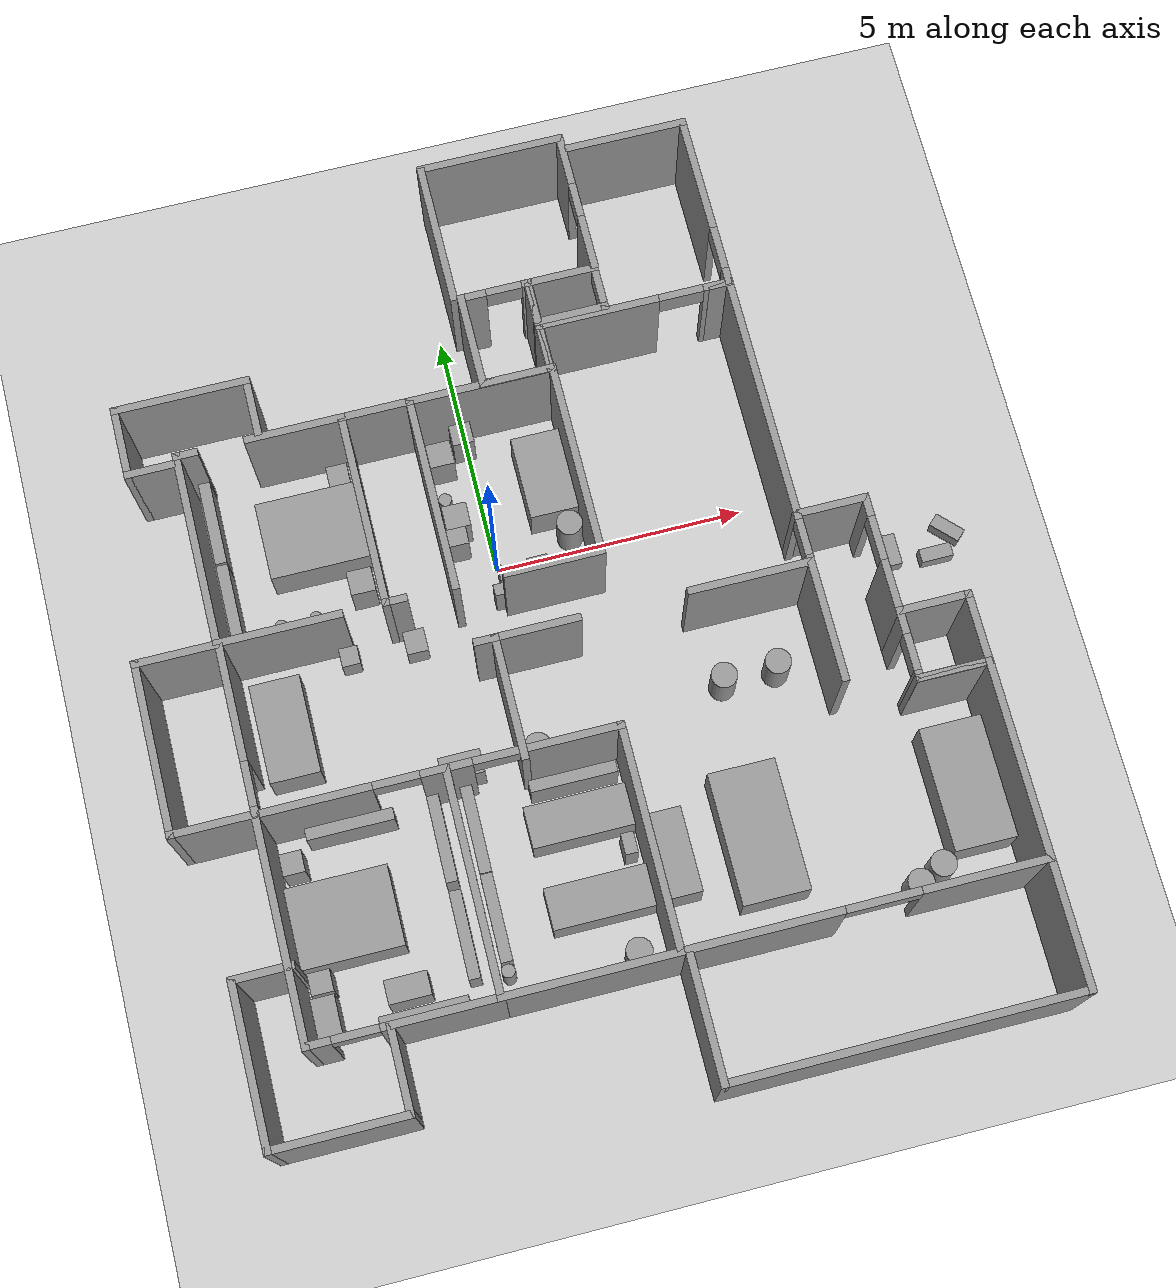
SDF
<sdf version="1.6">
 <world name="default">
  <light name="sun" type="directional">
   <pose>0 0 10 0 -0 0</pose>
   <diffuse>0.8 0.8 0.8 1</diffuse>
   <specular>0.1 0.1 0.1 1</specular>
   <attenuation>
    <range>1000</range>
    <constant>0.9</constant>
    <linear>0.01</linear>
    <quadratic>0.001</quadratic>
   </attenuation>
   <direction>-0.5 0.5 -1</direction>
  </light>
  <model name="ground_plane">
   <static>1</static>
   <link name="link">
    <collision name="collision">
     <geometry><plane><normal>0 0 1</normal><size>100 100</size></plane></geometry>
     <surface><friction><ode><mu>100</mu><mu2>50</mu2></ode></friction></surface>
    </collision>
    <visual name="visual">
     <cast_shadows>0</cast_shadows>
     <geometry><plane><normal>0 0 1</normal><size>100 100</size></plane></geometry>
     <material>
      <script><uri>file://media/materials/scripts/gazebo.material</uri><name>Gazebo/Grey</name></script>
     </material>
    </visual>
   </link>
  </model>
  <gravity>0 0 -9.8</gravity>
  <magnetic_field>6e-06 2.3e-05 -4.2e-05</magnetic_field>
  <atmosphere type="adiabatic"/>
  <physics name="default_physics" default="0" type="ode">
   <max_step_size>0.001</max_step_size>
   <real_time_factor>1</real_time_factor>
   <real_time_update_rate>1000</real_time_update_rate>
  </physics>
  <scene><ambient>0.4 0.4 0.4 1</ambient><background>0.7 0.7 0.7 1</background><shadows>1</shadows></scene>
  <spherical_coordinates>
   <surface_model>EARTH_WGS84</surface_model>
   <latitude_deg>0</latitude_deg>
   <longitude_deg>0</longitude_deg>
   <elevation>0</elevation>
   <heading_deg>0</heading_deg>
  </spherical_coordinates>
  <model name="cma_escritorio">
   <pose>-1.8304 1.03024 0 0 -0 0</pose>
   <link name="Wall_11">
    <collision name="Wall_11_Collision">
     <geometry><box><size>2 0.15 2.5</size></box></geometry>
     <pose>0 0 1.25 0 -0 0</pose>
    </collision>
    <visual name="Wall_11_Visual">
     <pose>0 0 1.25 0 -0 0</pose>
     <geometry><box><size>2 0.15 2.5</size></box></geometry>
     <material>
      <script><uri>file://media/materials/scripts/gazebo.material</uri><name>Gazebo/Grey</name></script>
      <ambient>1 1 1 1</ambient>
     </material>
    </visual>
    <pose>-1.4 1.93 0 0 -0 3.14159</pose>
   </link>
   <link name="Wall_2">
    <collision name="Wall_2_Collision">
     <geometry><box><size>4 0.15 2.5</size></box></geometry>
     <pose>0 0 1.25 0 -0 0</pose>
    </collision>
    <visual name="Wall_2_Visual">
     <pose>0 0 1.25 0 -0 0</pose>
     <geometry><box><size>4 0.15 2.5</size></box></geometry>
     <material>
      <script><uri>file://media/materials/scripts/gazebo.material</uri><name>Gazebo/Grey</name></script>
      <ambient>1 1 1 1</ambient>
     </material>
    </visual>
    <pose>0.875 0.005 0 0 -0 1.5708</pose>
   </link>
   <link name="Wall_25">
    <collision name="Wall_25_Collision">
     <geometry><box><size>2.5 0.15 2.5</size></box></geometry>
     <pose>0 0 1.25 0 -0 0</pose>
    </collision>
    <visual name="Wall_25_Visual">
     <pose>0 0 1.25 0 -0 0</pose>
     <geometry><box><size>2.5 0.15 2.5</size></box></geometry>
     <material>
      <script><uri>file://media/materials/scripts/gazebo.material</uri><name>Gazebo/Grey</name></script>
      <ambient>1 1 1 1</ambient>
     </material>
    </visual>
    <pose>-2.55 -1.93 0 0 -0 3.14159</pose>
   </link>
   <link name="Wall_26">
    <collision name="Wall_26_Collision">
     <geometry><box><size>4 0.15 2.5</size></box></geometry>
     <pose>0 0 1.25 0 -0 0</pose>
    </collision>
    <visual name="Wall_26_Visual">
     <pose>0 0 1.25 0 -0 0</pose>
     <geometry><box><size>4 0.15 2.5</size></box></geometry>
     <material>
      <script><uri>file://media/materials/scripts/gazebo.material</uri><name>Gazebo/Grey</name></script>
      <ambient>1 1 1 1</ambient>
     </material>
    </visual>
    <pose>-3.725 -0.005 0 0 -0 1.5708</pose>
   </link>
   <link name="Wall_27">
    <collision name="Wall_27_Collision">
     <geometry><box><size>0.5 0.15 2.5</size></box></geometry>
     <pose>0 0 1.25 0 -0 0</pose>
    </collision>
    <visual name="Wall_27_Visual">
     <pose>0 0 1.25 0 -0 0</pose>
     <geometry><box><size>0.5 0.15 2.5</size></box></geometry>
     <material>
      <script><uri>file://media/materials/scripts/gazebo.material</uri><name>Gazebo/Grey</name></script>
      <ambient>1 1 1 1</ambient>
     </material>
    </visual>
    <pose>-3.55 1.92 0 0 -0 0</pose>
   </link>
   <link name="Wall_3">
    <collision name="Wall_3_Collision">
     <geometry><box><size>3 0.15 2.5</size></box></geometry>
     <pose>0 0 1.25 0 -0 0</pose>
    </collision>
    <visual name="Wall_3_Visual">
     <pose>0 0 1.25 0 -0 0</pose>
     <geometry><box><size>3 0.15 2.5</size></box></geometry>
     <material>
      <script><uri>file://media/materials/scripts/gazebo.material</uri><name>Gazebo/Grey</name></script>
      <ambient>1 1 1 1</ambient>
     </material>
    </visual>
    <pose>2.3 1.93 0 0 -0 0</pose>
   </link>
   <link name="Wall_4">
    <collision name="Wall_4_Collision">
     <geometry><box><size>4 0.15 2.5</size></box></geometry>
     <pose>0 0 1.25 0 -0 0</pose>
    </collision>
    <visual name="Wall_4_Visual">
     <pose>0 0 1.25 0 -0 0</pose>
     <geometry><box><size>4 0.15 2.5</size></box></geometry>
     <material>
      <script><uri>file://media/materials/scripts/gazebo.material</uri><name>Gazebo/Grey</name></script>
      <ambient>1 1 1 1</ambient>
     </material>
    </visual>
    <pose>3.725 0.005 0 0 0 -1.5708</pose>
   </link>
   <link name="Wall_5">
    <collision name="Wall_5_Collision">
     <geometry><box><size>2 0.15 2.5</size></box></geometry>
     <pose>0 0 1.25 0 -0 0</pose>
    </collision>
    <visual name="Wall_5_Visual">
     <pose>0 0 1.25 0 -0 0</pose>
     <geometry><box><size>2 0.15 2.5</size></box></geometry>
     <material>
      <script><uri>file://media/materials/scripts/gazebo.material</uri><name>Gazebo/Grey</name></script>
      <ambient>1 1 1 1</ambient>
     </material>
    </visual>
    <pose>2.8 -1.92 0 0 -0 3.14159</pose>
   </link>
   <link name="Wall_7">
    <collision name="Wall_7_Collision">
     <geometry><box><size>1.5 0.15 2.5</size></box></geometry>
     <pose>0 0 1.25 0 -0 0</pose>
    </collision>
    <visual name="Wall_7_Visual">
     <pose>0 0 1.25 0 -0 0</pose>
     <geometry><box><size>1.5 0.15 2.5</size></box></geometry>
     <material>
      <script><uri>file://media/materials/scripts/gazebo.material</uri><name>Gazebo/Grey</name></script>
      <ambient>1 1 1 1</ambient>
     </material>
    </visual>
    <pose>0.2 1.93 0 0 -0 3.14159</pose>
   </link>
   <link name="Wall_8">
    <collision name="Wall_8_Collision">
     <geometry><box><size>4 0.15 2.5</size></box></geometry>
     <pose>0 0 1.25 0 -0 0</pose>
    </collision>
    <visual name="Wall_8_Visual">
     <pose>0 0 1.25 0 -0 0</pose>
     <geometry><box><size>4 0.15 2.5</size></box></geometry>
     <material>
      <script><uri>file://media/materials/scripts/gazebo.material</uri><name>Gazebo/Grey</name></script>
      <ambient>1 1 1 1</ambient>
     </material>
    </visual>
    <pose>-0.475 0.005 0 0 0 -1.5708</pose>
   </link>
   <link name="Wall_9">
    <collision name="Wall_9_Collision">
     <geometry><box><size>0.5 0.15 2.5</size></box></geometry>
     <pose>0 0 1.25 0 -0 0</pose>
    </collision>
    <visual name="Wall_9_Visual">
     <pose>0 0 1.25 0 -0 0</pose>
     <geometry><box><size>0.5 0.15 2.5</size></box></geometry>
     <material>
      <script><uri>file://media/materials/scripts/gazebo.material</uri><name>Gazebo/Grey</name></script>
      <ambient>1 1 1 1</ambient>
     </material>
    </visual>
    <pose>-0.3 -1.92 0 0 -0 0</pose>
   </link>
   <static>1</static>
  </model>
  <model name="cma_banheiro">
   <pose>-5.22928 3.4871 0 0 -0 0</pose>
   <link name="Wall_0">
    <collision name="Wall_0_Collision">
     <geometry><box><size>1 0.15 2.5</size></box></geometry>
     <pose>0 0 1.25 0 -0 0</pose>
    </collision>
    <visual name="Wall_0_Visual">
     <pose>0 0 1.25 0 -0 0</pose>
     <geometry><box><size>1 0.15 2.5</size></box></geometry>
     <material>
      <script><uri>file://media/materials/scripts/gazebo.material</uri><name>Gazebo/Grey</name></script>
      <ambient>1 1 1 1</ambient>
     </material>
    </visual>
    <pose>-0.875 -0.675 0 0 -0 3.14159</pose>
   </link>
   <link name="Wall_1">
    <collision name="Wall_1_Collision">
     <geometry><box><size>1.5 0.15 2.5</size></box></geometry>
     <pose>0 0 1.25 0 -0 0</pose>
    </collision>
    <visual name="Wall_1_Visual">
     <pose>0 0 1.25 0 -0 0</pose>
     <geometry><box><size>1.5 0.15 2.5</size></box></geometry>
     <material>
      <script><uri>file://media/materials/scripts/gazebo.material</uri><name>Gazebo/Grey</name></script>
      <ambient>1 1 1 1</ambient>
     </material>
    </visual>
    <pose>-1.3 0 0 0 -0 1.5708</pose>
   </link>
   <link name="Wall_2">
    <collision name="Wall_2_Collision">
     <geometry><box><size>2.75 0.15 2.5</size></box></geometry>
     <pose>0 0 1.25 0 -0 0</pose>
    </collision>
    <visual name="Wall_2_Visual">
     <pose>0 0 1.25 0 -0 0</pose>
     <geometry><box><size>2.75 0.15 2.5</size></box></geometry>
     <material>
      <script><uri>file://media/materials/scripts/gazebo.material</uri><name>Gazebo/Grey</name></script>
      <ambient>1 1 1 1</ambient>
     </material>
    </visual>
    <pose>0 0.675 0 0 -0 0</pose>
   </link>
   <link name="Wall_4">
    <collision name="Wall_4_Collision">
     <geometry><box><size>1.25 0.15 2.5</size></box></geometry>
     <pose>0 0 1.25 0 -0 0</pose>
    </collision>
    <visual name="Wall_4_Visual">
     <pose>0 0 1.25 0 -0 0</pose>
     <geometry><box><size>1.25 0.15 2.5</size></box></geometry>
     <material>
      <script><uri>file://media/materials/scripts/gazebo.material</uri><name>Gazebo/Grey</name></script>
      <ambient>1 1 1 1</ambient>
     </material>
    </visual>
    <pose>1.3 0.125 0 0 0 -1.5708</pose>
   </link>
   <static>1</static>
  </model>
  <model name="cma_varanda1">
   <pose>-6.32518 -2.59313 0 0 -0 0</pose>
   <link name="Wall_0">
    <pose>0.8 0 0 0 0 -1.5708</pose>
    <visual name="Wall_0_Visual_0">
     <pose>-0.5525 0 1.25 0 -0 0</pose>
     <geometry><box><size>2.395 0.15 2.5</size></box></geometry>
     <material>
      <script><uri>file://media/materials/scripts/gazebo.material</uri><name>Gazebo/Grey</name></script>
      <ambient>1 1 1 1</ambient>
     </material>
    </visual>
    <collision name="Wall_0_Collision_0">
     <geometry><box><size>2.395 0.15 2.5</size></box></geometry>
     <pose>-0.5525 0 1.25 0 -0 0</pose>
    </collision>
    <visual name="Wall_0_Visual_1">
     <pose>1.6375 0 1.25 0 -0 0</pose>
     <geometry><box><size>0.225 0.15 2.5</size></box></geometry>
     <material>
      <script><uri>file://media/materials/scripts/gazebo.material</uri><name>Gazebo/Grey</name></script>
      <ambient>1 1 1 1</ambient>
     </material>
    </visual>
    <collision name="Wall_0_Collision_1">
     <geometry><box><size>0.225 0.15 2.5</size></box></geometry>
     <pose>1.6375 0 1.25 0 -0 0</pose>
    </collision>
    <visual name="Wall_0_Visual_2">
     <pose>1.085 0 2.25 0 -0 0</pose>
     <geometry><box><size>0.88 0.15 0.5</size></box></geometry>
     <material>
      <script><uri>file://media/materials/scripts/gazebo.material</uri><name>Gazebo/Grey</name></script>
      <ambient>1 1 1 1</ambient>
     </material>
    </visual>
    <collision name="Wall_0_Collision_2">
     <geometry><box><size>0.88 0.15 0.5</size></box></geometry>
     <pose>1.085 0 2.25 0 -0 0</pose>
    </collision>
   </link>
   <link name="Wall_1">
    <collision name="Wall_1_Collision">
     <geometry><box><size>1.75 0.15 2.5</size></box></geometry>
     <pose>0 0 1.25 0 -0 0</pose>
    </collision>
    <visual name="Wall_1_Visual">
     <pose>0 0 1.25 0 -0 0</pose>
     <geometry><box><size>1.75 0.15 2.5</size></box></geometry>
     <material>
      <script><uri>file://media/materials/scripts/gazebo.material</uri><name>Gazebo/Grey</name></script>
      <ambient>1 1 1 1</ambient>
     </material>
    </visual>
    <pose>0 -1.675 0 0 -0 3.14159</pose>
   </link>
   <link name="Wall_2">
    <collision name="Wall_2_Collision">
     <geometry><box><size>3.5 0.15 2.5</size></box></geometry>
     <pose>0 0 1.25 0 -0 0</pose>
    </collision>
    <visual name="Wall_2_Visual">
     <pose>0 0 1.25 0 -0 0</pose>
     <geometry><box><size>3.5 0.15 2.5</size></box></geometry>
     <material>
      <script><uri>file://media/materials/scripts/gazebo.material</uri><name>Gazebo/Grey</name></script>
      <ambient>1 1 1 1</ambient>
     </material>
    </visual>
    <pose>-0.8 0 0 0 -0 1.5708</pose>
   </link>
   <link name="Wall_3">
    <collision name="Wall_3_Collision">
     <geometry><box><size>1.75 0.15 2.5</size></box></geometry>
     <pose>0 0 1.25 0 -0 0</pose>
    </collision>
    <visual name="Wall_3_Visual">
     <pose>0 0 1.25 0 -0 0</pose>
     <geometry><box><size>1.75 0.15 2.5</size></box></geometry>
     <material>
      <script><uri>file://media/materials/scripts/gazebo.material</uri><name>Gazebo/Grey</name></script>
      <ambient>1 1 1 1</ambient>
     </material>
    </visual>
    <pose>0 1.675 0 0 -0 0</pose>
   </link>
   <static>1</static>
  </model>
  <model name="cma_quartos">
   <pose>-2.58169 -7.26456 0 0 -0 0</pose>
   <link name="Wall_0">
    <collision name="Wall_0_Collision">
     <geometry><box><size>4.5 0.15 2.5</size></box></geometry>
     <pose>0 0 1.25 0 -0 0</pose>
    </collision>
    <visual name="Wall_0_Visual">
     <pose>0 0 1.25 0 -0 0</pose>
     <geometry><box><size>4.5 0.15 2.5</size></box></geometry>
     <material>
      <script><uri>file://media/materials/scripts/gazebo.material</uri><name>Gazebo/Grey</name></script>
      <ambient>1 1 1 1</ambient>
     </material>
    </visual>
    <pose>0.645 0.81 0 0 0 -1.5708</pose>
   </link>
   <link name="Wall_1">
    <pose>-1.155 -1.365 0 0 -0 3.14159</pose>
    <visual name="Wall_1_Visual_0">
     <pose>-0.7225 0 1.25 0 -0 0</pose>
     <geometry><box><size>2.305 0.15 2.5</size></box></geometry>
     <material>
      <script><uri>file://media/materials/scripts/gazebo.material</uri><name>Gazebo/Grey</name></script>
      <ambient>1 1 1 1</ambient>
     </material>
    </visual>
    <collision name="Wall_1_Collision_0">
     <geometry><box><size>2.305 0.15 2.5</size></box></geometry>
     <pose>-0.7225 0 1.25 0 -0 0</pose>
    </collision>
    <visual name="Wall_1_Visual_1">
     <pose>1.6025 0 1.25 0 -0 0</pose>
     <geometry><box><size>0.545 0.15 2.5</size></box></geometry>
     <material>
      <script><uri>file://media/materials/scripts/gazebo.material</uri><name>Gazebo/Grey</name></script>
      <ambient>1 1 1 1</ambient>
     </material>
    </visual>
    <collision name="Wall_1_Collision_1">
     <geometry><box><size>0.545 0.15 2.5</size></box></geometry>
     <pose>1.6025 0 1.25 0 -0 0</pose>
    </collision>
    <visual name="Wall_1_Visual_2">
     <pose>0.88 0 2.25 0 -0 0</pose>
     <geometry><box><size>0.9 0.15 0.5</size></box></geometry>
     <material>
      <script><uri>file://media/materials/scripts/gazebo.material</uri><name>Gazebo/Grey</name></script>
      <ambient>1 1 1 1</ambient>
     </material>
    </visual>
    <collision name="Wall_1_Collision_2">
     <geometry><box><size>0.9 0.15 0.5</size></box></geometry>
     <pose>0.88 0 2.25 0 -0 0</pose>
    </collision>
   </link>
   <link name="Wall_10">
    <collision name="Wall_10_Collision">
     <geometry><box><size>1.75 0.15 2.5</size></box></geometry>
     <pose>0 0 1.25 0 -0 0</pose>
    </collision>
    <visual name="Wall_10_Visual">
     <pose>0 0 1.25 0 -0 0</pose>
     <geometry><box><size>1.75 0.15 2.5</size></box></geometry>
     <material>
      <script><uri>file://media/materials/scripts/gazebo.material</uri><name>Gazebo/Grey</name></script>
      <ambient>1 1 1 1</ambient>
     </material>
    </visual>
    <pose>-1.395 -2.185 0 0 0 -1.5708</pose>
   </link>
   <link name="Wall_11">
    <collision name="Wall_11_Collision">
     <geometry><box><size>2.75 0.15 2.5</size></box></geometry>
     <pose>0 0 1.25 0 -0 0</pose>
    </collision>
    <visual name="Wall_11_Visual">
     <pose>0 0 1.25 0 -0 0</pose>
     <geometry><box><size>2.75 0.15 2.5</size></box></geometry>
     <material>
      <script><uri>file://media/materials/scripts/gazebo.material</uri><name>Gazebo/Grey</name></script>
      <ambient>1 1 1 1</ambient>
     </material>
    </visual>
    <pose>-2.695 -2.985 0 0 -0 3.14159</pose>
   </link>
   <link name="Wall_12">
    <collision name="Wall_12_Collision">
     <geometry><box><size>3.25 0.15 2.5</size></box></geometry>
     <pose>0 0 1.25 0 -0 0</pose>
    </collision>
    <visual name="Wall_12_Visual">
     <pose>0 0 1.25 0 -0 0</pose>
     <geometry><box><size>3.25 0.15 2.5</size></box></geometry>
     <material>
      <script><uri>file://media/materials/scripts/gazebo.material</uri><name>Gazebo/Grey</name></script>
      <ambient>1 1 1 1</ambient>
     </material>
    </visual>
    <pose>-3.995 -1.435 0 0 -0 1.5708</pose>
   </link>
   <link name="Wall_13">
    <collision name="Wall_13_Collision">
     <geometry><box><size>1.25 0.15 2.5</size></box></geometry>
     <pose>0 0 1.25 0 -0 0</pose>
    </collision>
    <visual name="Wall_13_Visual">
     <pose>0 0 1.25 0 -0 0</pose>
     <geometry><box><size>1.25 0.15 2.5</size></box></geometry>
     <material>
      <script><uri>file://media/materials/scripts/gazebo.material</uri><name>Gazebo/Grey</name></script>
      <ambient>1 1 1 1</ambient>
     </material>
    </visual>
    <pose>-3.445 0.115 0 0 -0 0</pose>
   </link>
   <link name="Wall_2">
    <collision name="Wall_2_Collision">
     <geometry><box><size>4.5 0.15 2.5</size></box></geometry>
     <pose>0 0 1.25 0 -0 0</pose>
    </collision>
    <visual name="Wall_2_Visual">
     <pose>0 0 1.25 0 -0 0</pose>
     <geometry><box><size>4.5 0.15 2.5</size></box></geometry>
     <material>
      <script><uri>file://media/materials/scripts/gazebo.material</uri><name>Gazebo/Grey</name></script>
      <ambient>1 1 1 1</ambient>
     </material>
    </visual>
    <pose>-2.955 0.81 0 0 -0 1.5708</pose>
   </link>
   <link name="Wall_3">
    <pose>-1.155 2.985 0 0 -0 0</pose>
    <visual name="Wall_3_Visual_0">
     <pose>-0.7325 0 1.25 0 -0 0</pose>
     <geometry><box><size>2.285 0.15 2.5</size></box></geometry>
     <material>
      <script><uri>file://media/materials/scripts/gazebo.material</uri><name>Gazebo/Grey</name></script>
      <ambient>1 1 1 1</ambient>
     </material>
    </visual>
    <collision name="Wall_3_Collision_0">
     <geometry><box><size>2.285 0.15 2.5</size></box></geometry>
     <pose>-0.7325 0 1.25 0 -0 0</pose>
    </collision>
    <visual name="Wall_3_Visual_1">
     <pose>1.5925 0 1.25 0 -0 0</pose>
     <geometry><box><size>0.565 0.15 2.5</size></box></geometry>
     <material>
      <script><uri>file://media/materials/scripts/gazebo.material</uri><name>Gazebo/Grey</name></script>
      <ambient>1 1 1 1</ambient>
     </material>
    </visual>
    <collision name="Wall_3_Collision_1">
     <geometry><box><size>0.565 0.15 2.5</size></box></geometry>
     <pose>1.5925 0 1.25 0 -0 0</pose>
    </collision>
    <visual name="Wall_3_Visual_2">
     <pose>0.86 0 2.25 0 -0 0</pose>
     <geometry><box><size>0.9 0.15 0.5</size></box></geometry>
     <material>
      <script><uri>file://media/materials/scripts/gazebo.material</uri><name>Gazebo/Grey</name></script>
      <ambient>1 1 1 1</ambient>
     </material>
    </visual>
    <collision name="Wall_3_Collision_2">
     <geometry><box><size>0.9 0.15 0.5</size></box></geometry>
     <pose>0.86 0 2.25 0 -0 0</pose>
    </collision>
   </link>
   <link name="Wall_6">
    <pose>2.32 2.985 0 0 -0 0</pose>
    <visual name="Wall_6_Visual_0">
     <pose>-1.4575 0 1.25 0 -0 0</pose>
     <geometry><box><size>0.585 0.15 2.5</size></box></geometry>
     <material>
      <script><uri>file://media/materials/scripts/gazebo.material</uri><name>Gazebo/Grey</name></script>
      <ambient>1 1 1 1</ambient>
     </material>
    </visual>
    <collision name="Wall_6_Collision_0">
     <geometry><box><size>0.585 0.15 2.5</size></box></geometry>
     <pose>-1.4575 0 1.25 0 -0 0</pose>
    </collision>
    <visual name="Wall_6_Visual_1">
     <pose>0.7425 0 1.25 0 -0 0</pose>
     <geometry><box><size>2.015 0.15 2.5</size></box></geometry>
     <material>
      <script><uri>file://media/materials/scripts/gazebo.material</uri><name>Gazebo/Grey</name></script>
      <ambient>1 1 1 1</ambient>
     </material>
    </visual>
    <collision name="Wall_6_Collision_1">
     <geometry><box><size>2.015 0.15 2.5</size></box></geometry>
     <pose>0.7425 0 1.25 0 -0 0</pose>
    </collision>
    <visual name="Wall_6_Visual_2">
     <pose>-0.715 0 2.25 0 -0 0</pose>
     <geometry><box><size>0.9 0.15 0.5</size></box></geometry>
     <material>
      <script><uri>file://media/materials/scripts/gazebo.material</uri><name>Gazebo/Grey</name></script>
      <ambient>1 1 1 1</ambient>
     </material>
    </visual>
    <collision name="Wall_6_Collision_2">
     <geometry><box><size>0.9 0.15 0.5</size></box></geometry>
     <pose>-0.715 0 2.25 0 -0 0</pose>
    </collision>
   </link>
   <link name="Wall_7">
    <collision name="Wall_7_Collision">
     <geometry><box><size>4.5 0.15 2.5</size></box></geometry>
     <pose>0 0 1.25 0 -0 0</pose>
    </collision>
    <visual name="Wall_7_Visual">
     <pose>0 0 1.25 0 -0 0</pose>
     <geometry><box><size>4.5 0.15 2.5</size></box></geometry>
     <material>
      <script><uri>file://media/materials/scripts/gazebo.material</uri><name>Gazebo/Grey</name></script>
      <ambient>1 1 1 1</ambient>
     </material>
    </visual>
    <pose>3.995 0.81 0 0 0 -1.5708</pose>
   </link>
   <link name="Wall_8">
    <collision name="Wall_8_Collision">
     <geometry><box><size>3.5 0.15 2.5</size></box></geometry>
     <pose>0 0 1.25 0 -0 0</pose>
    </collision>
    <visual name="Wall_8_Visual">
     <pose>0 0 1.25 0 -0 0</pose>
     <geometry><box><size>3.5 0.15 2.5</size></box></geometry>
     <material>
      <script><uri>file://media/materials/scripts/gazebo.material</uri><name>Gazebo/Grey</name></script>
      <ambient>1 1 1 1</ambient>
     </material>
    </visual>
    <pose>2.32 -1.365 0 0 -0 3.14159</pose>
   </link>
   <static>1</static>
  </model>
  <model name="cma_parede_t">
   <pose>0.159955 -3.24016 0 0 -0 0</pose>
   <link name="Wall_15">
    <collision name="Wall_15_Collision">
     <geometry><box><size>2.5 0.15 2.5</size></box></geometry>
     <pose>0 0 1.25 0 -0 0</pose>
    </collision>
    <visual name="Wall_15_Visual">
     <pose>0 0 1.25 0 -0 0</pose>
     <geometry><box><size>2.5 0.15 2.5</size></box></geometry>
     <material>
      <script><uri>file://media/materials/scripts/gazebo.material</uri><name>Gazebo/Grey</name></script>
      <ambient>1 1 1 1</ambient>
     </material>
    </visual>
    <pose>-0.625 0 0 0 -0 1.5708</pose>
   </link>
   <link name="Wall_16">
    <collision name="Wall_16_Collision">
     <geometry><box><size>0.5 0.15 2.5</size></box></geometry>
     <pose>0 0 1.25 0 -0 0</pose>
    </collision>
    <visual name="Wall_16_Visual">
     <pose>0 0 1.25 0 -0 0</pose>
     <geometry><box><size>0.5 0.15 2.5</size></box></geometry>
     <material>
      <script><uri>file://media/materials/scripts/gazebo.material</uri><name>Gazebo/Grey</name></script>
      <ambient>1 1 1 1</ambient>
     </material>
    </visual>
    <pose>-0.8 1.175 0 0 -0 3.14159</pose>
   </link>
   <link name="Wall_18">
    <collision name="Wall_18_Collision">
     <geometry><box><size>1.75 0.15 2.5</size></box></geometry>
     <pose>0 0 1.25 0 -0 0</pose>
    </collision>
    <visual name="Wall_18_Visual">
     <pose>0 0 1.25 0 -0 0</pose>
     <geometry><box><size>1.75 0.15 2.5</size></box></geometry>
     <material>
      <script><uri>file://media/materials/scripts/gazebo.material</uri><name>Gazebo/Grey</name></script>
      <ambient>1 1 1 1</ambient>
     </material>
    </visual>
    <pose>0.175 1.175 0 0 -0 0</pose>
   </link>
   <static>1</static>
  </model>
  <model name="cma_parede_L">
   <pose>4.97628 -6.69992 0 0 -0 0</pose>
   <link name="Wall_0">
    <pose>0 -1.925 0 0 -0 0</pose>
    <visual name="Wall_0_Visual_0">
     <pose>-1.985 0 1.25 0 -0 0</pose>
     <geometry><box><size>3.03 0.15 2.5</size></box></geometry>
     <material>
      <script><uri>file://media/materials/scripts/gazebo.material</uri><name>Gazebo/Grey</name></script>
      <ambient>1 1 1 1</ambient>
     </material>
    </visual>
    <collision name="Wall_0_Collision_0">
     <geometry><box><size>3.03 0.15 2.5</size></box></geometry>
     <pose>-1.985 0 1.25 0 -0 0</pose>
    </collision>
    <visual name="Wall_0_Visual_1">
     <pose>2.24 0 1.25 0 -0 0</pose>
     <geometry><box><size>2.52 0.15 2.5</size></box></geometry>
     <material>
      <script><uri>file://media/materials/scripts/gazebo.material</uri><name>Gazebo/Grey</name></script>
      <ambient>1 1 1 1</ambient>
     </material>
    </visual>
    <collision name="Wall_0_Collision_1">
     <geometry><box><size>2.52 0.15 2.5</size></box></geometry>
     <pose>2.24 0 1.25 0 -0 0</pose>
    </collision>
    <visual name="Wall_0_Visual_2">
     <pose>0.255 0 2.25 0 -0 0</pose>
     <geometry><box><size>1.45 0.15 0.5</size></box></geometry>
     <material>
      <script><uri>file://media/materials/scripts/gazebo.material</uri><name>Gazebo/Grey</name></script>
      <ambient>1 1 1 1</ambient>
     </material>
    </visual>
    <collision name="Wall_0_Collision_2">
     <geometry><box><size>1.45 0.15 0.5</size></box></geometry>
     <pose>0.255 0 2.25 0 -0 0</pose>
    </collision>
   </link>
   <link name="Wall_1">
    <collision name="Wall_1_Collision">
     <geometry><box><size>4 0.15 2.5</size></box></geometry>
     <pose>0 0 1.25 0 -0 0</pose>
    </collision>
    <visual name="Wall_1_Visual">
     <pose>0 0 1.25 0 -0 0</pose>
     <geometry><box><size>4 0.15 2.5</size></box></geometry>
     <material>
      <script><uri>file://media/materials/scripts/gazebo.material</uri><name>Gazebo/Grey</name></script>
      <ambient>1 1 1 1</ambient>
     </material>
    </visual>
    <pose>3.425 0 0 0 -0 1.5708</pose>
   </link>
   <link name="Wall_2">
    <collision name="Wall_2_Collision">
     <geometry><box><size>1.5 0.15 2.5</size></box></geometry>
     <pose>0 0 1.25 0 -0 0</pose>
    </collision>
    <visual name="Wall_2_Visual">
     <pose>0 0 1.25 0 -0 0</pose>
     <geometry><box><size>1.5 0.15 2.5</size></box></geometry>
     <material>
      <script><uri>file://media/materials/scripts/gazebo.material</uri><name>Gazebo/Grey</name></script>
      <ambient>1 1 1 1</ambient>
     </material>
    </visual>
    <pose>2.75 1.925 0 0 -0 3.14159</pose>
   </link>
   <static>1</static>
  </model>
  <model name="cma_lavabo">
   <pose>7.72297 -4.09302 0 0 -0 0</pose>
   <link name="Wall_4">
    <pose>-0.675 0 0 0 -0 1.5708</pose>
    <visual name="Wall_4_Visual_0">
     <pose>-0.635 0 1.25 0 -0 0</pose>
     <geometry><box><size>0.23 0.15 2.5</size></box></geometry>
     <material>
      <script><uri>file://media/materials/scripts/gazebo.material</uri><name>Gazebo/Grey</name></script>
      <ambient>1 1 1 1</ambient>
     </material>
    </visual>
    <collision name="Wall_4_Collision_0">
     <geometry><box><size>0.23 0.15 2.5</size></box></geometry>
     <pose>-0.635 0 1.25 0 -0 0</pose>
    </collision>
    <visual name="Wall_4_Visual_1">
     <pose>0.48 0 1.25 0 -0 0</pose>
     <geometry><box><size>0.54 0.15 2.5</size></box></geometry>
     <material>
      <script><uri>file://media/materials/scripts/gazebo.material</uri><name>Gazebo/Grey</name></script>
      <ambient>1 1 1 1</ambient>
     </material>
    </visual>
    <collision name="Wall_4_Collision_1">
     <geometry><box><size>0.54 0.15 2.5</size></box></geometry>
     <pose>0.48 0 1.25 0 -0 0</pose>
    </collision>
    <visual name="Wall_4_Visual_2">
     <pose>-0.155 0 2.25 0 -0 0</pose>
     <geometry><box><size>0.73 0.15 0.5</size></box></geometry>
     <material>
      <script><uri>file://media/materials/scripts/gazebo.material</uri><name>Gazebo/Grey</name></script>
      <ambient>1 1 1 1</ambient>
     </material>
    </visual>
    <collision name="Wall_4_Collision_2">
     <geometry><box><size>0.73 0.15 0.5</size></box></geometry>
     <pose>-0.155 0 2.25 0 -0 0</pose>
    </collision>
   </link>
   <link name="Wall_5">
    <collision name="Wall_5_Collision">
     <geometry><box><size>1.5 0.15 2.5</size></box></geometry>
     <pose>0 0 1.25 0 -0 0</pose>
    </collision>
    <visual name="Wall_5_Visual">
     <pose>0 0 1.25 0 -0 0</pose>
     <geometry><box><size>1.5 0.15 2.5</size></box></geometry>
     <material>
      <script><uri>file://media/materials/scripts/gazebo.material</uri><name>Gazebo/Grey</name></script>
      <ambient>1 1 1 1</ambient>
     </material>
    </visual>
    <pose>0 0.675 0 0 -0 0</pose>
   </link>
   <link name="Wall_6">
    <collision name="Wall_6_Collision">
     <geometry><box><size>1.5 0.15 2.5</size></box></geometry>
     <pose>0 0 1.25 0 -0 0</pose>
    </collision>
    <visual name="Wall_6_Visual">
     <pose>0 0 1.25 0 -0 0</pose>
     <geometry><box><size>1.5 0.15 2.5</size></box></geometry>
     <material>
      <script><uri>file://media/materials/scripts/gazebo.material</uri><name>Gazebo/Grey</name></script>
      <ambient>1 1 1 1</ambient>
     </material>
    </visual>
    <pose>0.675 0 0 0 0 -1.5708</pose>
   </link>
   <link name="Wall_7">
    <collision name="Wall_7_Collision">
     <geometry><box><size>1.5 0.15 2.5</size></box></geometry>
     <pose>0 0 1.25 0 -0 0</pose>
    </collision>
    <visual name="Wall_7_Visual">
     <pose>0 0 1.25 0 -0 0</pose>
     <geometry><box><size>1.5 0.15 2.5</size></box></geometry>
     <material>
      <script><uri>file://media/materials/scripts/gazebo.material</uri><name>Gazebo/Grey</name></script>
      <ambient>1 1 1 1</ambient>
     </material>
    </visual>
    <pose>0 -0.675 0 0 -0 3.14159</pose>
   </link>
   <static>1</static>
  </model>
  <model name="cma_L2">
   <pose>4.51683 -3.24587 0 0 -0 0</pose>
   <link name="Wall_10">
    <collision name="Wall_10_Collision">
     <geometry><box><size>2.5 0.15 2.5</size></box></geometry>
     <pose>0 0 1.25 0 -0 0</pose>
    </collision>
    <visual name="Wall_10_Visual">
     <pose>0 0 1.25 0 -0 0</pose>
     <geometry><box><size>2.5 0.15 2.5</size></box></geometry>
     <material>
      <script><uri>file://media/materials/scripts/gazebo.material</uri><name>Gazebo/Grey</name></script>
      <ambient>1 1 1 1</ambient>
     </material>
    </visual>
    <pose>1.175 0 0 0 0 -1.5708</pose>
   </link>
   <link name="Wall_9">
    <collision name="Wall_9_Collision">
     <geometry><box><size>2.5 0.15 2.5</size></box></geometry>
     <pose>0 0 1.25 0 -0 0</pose>
    </collision>
    <visual name="Wall_9_Visual">
     <pose>0 0 1.25 0 -0 0</pose>
     <geometry><box><size>2.5 0.15 2.5</size></box></geometry>
     <material>
      <script><uri>file://media/materials/scripts/gazebo.material</uri><name>Gazebo/Grey</name></script>
      <ambient>1 1 1 1</ambient>
     </material>
    </visual>
    <pose>0 1.175 0 0 -0 0</pose>
   </link>
   <static>1</static>
  </model>
  <model name="cma_L3">
   <pose>6.37221 -2.26022 0 0 -0 0</pose>
   <link name="Wall_12">
    <pose>-0.675 0.75 0 0 -0 1.5708</pose>
    <visual name="Wall_12_Visual_0">
     <pose>-0.46 0 1.25 0 -0 0</pose>
     <geometry><box><size>0.08 0.15 2.5</size></box></geometry>
     <material>
      <script><uri>file://media/materials/scripts/gazebo.material</uri><name>Gazebo/Grey</name></script>
      <ambient>1 1 1 1</ambient>
     </material>
    </visual>
    <collision name="Wall_12_Collision_0">
     <geometry><box><size>0.08 0.15 2.5</size></box></geometry>
     <pose>-0.46 0 1.25 0 -0 0</pose>
    </collision>
    <visual name="Wall_12_Visual_1">
     <pose>0.405 0 1.25 0 -0 0</pose>
     <geometry><box><size>0.19 0.15 2.5</size></box></geometry>
     <material>
      <script><uri>file://media/materials/scripts/gazebo.material</uri><name>Gazebo/Grey</name></script>
      <ambient>1 1 1 1</ambient>
     </material>
    </visual>
    <collision name="Wall_12_Collision_1">
     <geometry><box><size>0.19 0.15 2.5</size></box></geometry>
     <pose>0.405 0 1.25 0 -0 0</pose>
    </collision>
    <visual name="Wall_12_Visual_2">
     <pose>-0.055 0 2.25 0 -0 0</pose>
     <geometry><box><size>0.73 0.15 0.5</size></box></geometry>
     <material>
      <script><uri>file://media/materials/scripts/gazebo.material</uri><name>Gazebo/Grey</name></script>
      <ambient>1 1 1 1</ambient>
     </material>
    </visual>
    <collision name="Wall_12_Collision_2">
     <geometry><box><size>0.73 0.15 0.5</size></box></geometry>
     <pose>-0.055 0 2.25 0 -0 0</pose>
    </collision>
   </link>
   <link name="Wall_13">
    <collision name="Wall_13_Collision">
     <geometry><box><size>1.5 0.15 2.5</size></box></geometry>
     <pose>0 0 1.25 0 -0 0</pose>
    </collision>
    <visual name="Wall_13_Visual">
     <pose>0 0 1.25 0 -0 0</pose>
     <geometry><box><size>1.5 0.15 2.5</size></box></geometry>
     <material>
      <script><uri>file://media/materials/scripts/gazebo.material</uri><name>Gazebo/Grey</name></script>
      <ambient>1 1 1 1</ambient>
     </material>
    </visual>
    <pose>0 1.175 0 0 -0 0</pose>
   </link>
   <link name="Wall_14">
    <pose>0.675 0 0 0 0 -1.5708</pose>
    <visual name="Wall_14_Visual_0">
     <pose>-1.0175 0 1.25 0 -0 0</pose>
     <geometry><box><size>0.465 0.15 2.5</size></box></geometry>
     <material>
      <script><uri>file://media/materials/scripts/gazebo.material</uri><name>Gazebo/Grey</name></script>
      <ambient>1 1 1 1</ambient>
     </material>
    </visual>
    <collision name="Wall_14_Collision_0">
     <geometry><box><size>0.465 0.15 2.5</size></box></geometry>
     <pose>-1.0175 0 1.25 0 -0 0</pose>
    </collision>
    <visual name="Wall_14_Visual_1">
     <pose>0.6825 0 1.25 0 -0 0</pose>
     <geometry><box><size>1.135 0.15 2.5</size></box></geometry>
     <material>
      <script><uri>file://media/materials/scripts/gazebo.material</uri><name>Gazebo/Grey</name></script>
      <ambient>1 1 1 1</ambient>
     </material>
    </visual>
    <collision name="Wall_14_Collision_1">
     <geometry><box><size>1.135 0.15 2.5</size></box></geometry>
     <pose>0.6825 0 1.25 0 -0 0</pose>
    </collision>
    <visual name="Wall_14_Visual_2">
     <pose>-0.335 0 2.25 0 -0 0</pose>
     <geometry><box><size>0.9 0.15 0.5</size></box></geometry>
     <material>
      <script><uri>file://media/materials/scripts/gazebo.material</uri><name>Gazebo/Grey</name></script>
      <ambient>1 1 1 1</ambient>
     </material>
    </visual>
    <collision name="Wall_14_Collision_2">
     <geometry><box><size>0.9 0.15 0.5</size></box></geometry>
     <pose>-0.335 0 2.25 0 -0 0</pose>
    </collision>
   </link>
   <static>1</static>
  </model>
  <model name="cma_U">
   <pose>4.97895 -9.92408 0 0 -0 0</pose>
   <link name="Wall_16">
    <collision name="Wall_16_Collision">
     <geometry><box><size>2.5 0.15 2.5</size></box></geometry>
     <pose>0 0 1.25 0 -0 0</pose>
    </collision>
    <visual name="Wall_16_Visual">
     <pose>0 0 1.25 0 -0 0</pose>
     <geometry><box><size>2.5 0.15 2.5</size></box></geometry>
     <material>
      <script><uri>file://media/materials/scripts/gazebo.material</uri><name>Gazebo/Grey</name></script>
      <ambient>1 1 1 1</ambient>
     </material>
    </visual>
    <pose>-3.425 0 0 0 0 -1.5708</pose>
   </link>
   <link name="Wall_17">
    <collision name="Wall_17_Collision">
     <geometry><box><size>7 0.15 2.5</size></box></geometry>
     <pose>0 0 1.25 0 -0 0</pose>
    </collision>
    <visual name="Wall_17_Visual">
     <pose>0 0 1.25 0 -0 0</pose>
     <geometry><box><size>7 0.15 2.5</size></box></geometry>
     <material>
      <script><uri>file://media/materials/scripts/gazebo.material</uri><name>Gazebo/Grey</name></script>
      <ambient>1 1 1 1</ambient>
     </material>
    </visual>
    <pose>0 -1.175 0 0 -0 0</pose>
   </link>
   <link name="Wall_18">
    <collision name="Wall_18_Collision">
     <geometry><box><size>2.5 0.15 2.5</size></box></geometry>
     <pose>0 0 1.25 0 -0 0</pose>
    </collision>
    <visual name="Wall_18_Visual">
     <pose>0 0 1.25 0 -0 0</pose>
     <geometry><box><size>2.5 0.15 2.5</size></box></geometry>
     <material>
      <script><uri>file://media/materials/scripts/gazebo.material</uri><name>Gazebo/Grey</name></script>
      <ambient>1 1 1 1</ambient>
     </material>
    </visual>
    <pose>3.425 0 0 0 -0 1.5708</pose>
   </link>
   <static>1</static>
  </model>
  <model name="cma_L5">
   <pose>3.77502 1.45512 0 0 -0 0</pose>
   <link name="Wall_0">
    <collision name="Wall_0_Collision">
     <geometry><box><size>1 0.15 2.5</size></box></geometry>
     <pose>0 0 1.25 0 -0 0</pose>
    </collision>
    <visual name="Wall_0_Visual">
     <pose>0 0 1.25 0 -0 0</pose>
     <geometry><box><size>1 0.15 2.5</size></box></geometry>
     <material>
      <script><uri>file://media/materials/scripts/gazebo.material</uri><name>Gazebo/Grey</name></script>
      <ambient>1 1 1 1</ambient>
     </material>
    </visual>
    <pose>-1.925 2 0 0 -0 1.5708</pose>
   </link>
   <link name="Wall_1">
    <pose>0 2.425 0 0 -0 0</pose>
    <visual name="Wall_1_Visual_0">
     <pose>-0.7525 0 1.25 0 -0 0</pose>
     <geometry><box><size>2.495 0.15 2.5</size></box></geometry>
     <material>
      <script><uri>file://media/materials/scripts/gazebo.material</uri><name>Gazebo/Grey</name></script>
      <ambient>1 1 1 1</ambient>
     </material>
    </visual>
    <collision name="Wall_1_Collision_0">
     <geometry><box><size>2.495 0.15 2.5</size></box></geometry>
     <pose>-0.7525 0 1.25 0 -0 0</pose>
    </collision>
    <visual name="Wall_1_Visual_1">
     <pose>1.6975 0 1.25 0 -0 0</pose>
     <geometry><box><size>0.605 0.15 2.5</size></box></geometry>
     <material>
      <script><uri>file://media/materials/scripts/gazebo.material</uri><name>Gazebo/Grey</name></script>
      <ambient>1 1 1 1</ambient>
     </material>
    </visual>
    <collision name="Wall_1_Collision_1">
     <geometry><box><size>0.605 0.15 2.5</size></box></geometry>
     <pose>1.6975 0 1.25 0 -0 0</pose>
    </collision>
    <visual name="Wall_1_Visual_2">
     <pose>0.945 0 2.25 0 -0 0</pose>
     <geometry><box><size>0.9 0.15 0.5</size></box></geometry>
     <material>
      <script><uri>file://media/materials/scripts/gazebo.material</uri><name>Gazebo/Grey</name></script>
      <ambient>1 1 1 1</ambient>
     </material>
    </visual>
    <collision name="Wall_1_Collision_2">
     <geometry><box><size>0.9 0.15 0.5</size></box></geometry>
     <pose>0.945 0 2.25 0 -0 0</pose>
    </collision>
   </link>
   <link name="Wall_3">
    <collision name="Wall_3_Collision">
     <geometry><box><size>5 0.15 2.5</size></box></geometry>
     <pose>0 0 1.25 0 -0 0</pose>
    </collision>
    <visual name="Wall_3_Visual">
     <pose>0 0 1.25 0 -0 0</pose>
     <geometry><box><size>5 0.15 2.5</size></box></geometry>
     <material>
      <script><uri>file://media/materials/scripts/gazebo.material</uri><name>Gazebo/Grey</name></script>
      <ambient>1 1 1 1</ambient>
     </material>
    </visual>
    <pose>1.925 0 0 0 0 -1.5708</pose>
   </link>
   <static>1</static>
  </model>
  <model name="cma_dispensa">
   <pose>2.52584 4.40119 0 0 -0 0</pose>
   <link name="Wall_5">
    <collision name="Wall_5_Collision">
     <geometry><box><size>1 0.15 2.5</size></box></geometry>
     <pose>0 0 1.25 0 -0 0</pose>
    </collision>
    <visual name="Wall_5_Visual">
     <pose>0 0 1.25 0 -0 0</pose>
     <geometry><box><size>1 0.15 2.5</size></box></geometry>
     <material>
      <script><uri>file://media/materials/scripts/gazebo.material</uri><name>Gazebo/Grey</name></script>
      <ambient>1 1 1 1</ambient>
     </material>
    </visual>
    <pose>-0.675 0 0 0 -0 1.5708</pose>
   </link>
   <link name="Wall_6">
    <collision name="Wall_6_Collision">
     <geometry><box><size>1.5 0.15 2.5</size></box></geometry>
     <pose>0 0 1.25 0 -0 0</pose>
    </collision>
    <visual name="Wall_6_Visual">
     <pose>0 0 1.25 0 -0 0</pose>
     <geometry><box><size>1.5 0.15 2.5</size></box></geometry>
     <material>
      <script><uri>file://media/materials/scripts/gazebo.material</uri><name>Gazebo/Grey</name></script>
      <ambient>1 1 1 1</ambient>
     </material>
    </visual>
    <pose>0 0.425 0 0 -0 0</pose>
   </link>
   <link name="Wall_7">
    <pose>0.675 0 0 0 0 -1.5708</pose>
    <visual name="Wall_7_Visual_0">
     <pose>-0.4275 0 1.25 0 -0 0</pose>
     <geometry><box><size>0.145 0.15 2.5</size></box></geometry>
     <material>
      <script><uri>file://media/materials/scripts/gazebo.material</uri><name>Gazebo/Grey</name></script>
      <ambient>1 1 1 1</ambient>
     </material>
    </visual>
    <collision name="Wall_7_Collision_0">
     <geometry><box><size>0.145 0.15 2.5</size></box></geometry>
     <pose>-0.4275 0 1.25 0 -0 0</pose>
    </collision>
    <visual name="Wall_7_Visual_1">
     <pose>0.4225 0 1.25 0 -0 0</pose>
     <geometry><box><size>0.155 0.15 2.5</size></box></geometry>
     <material>
      <script><uri>file://media/materials/scripts/gazebo.material</uri><name>Gazebo/Grey</name></script>
      <ambient>1 1 1 1</ambient>
     </material>
    </visual>
    <collision name="Wall_7_Collision_1">
     <geometry><box><size>0.155 0.15 2.5</size></box></geometry>
     <pose>0.4225 0 1.25 0 -0 0</pose>
    </collision>
    <visual name="Wall_7_Visual_2">
     <pose>-0.005 0 2.25 0 -0 0</pose>
     <geometry><box><size>0.7 0.15 0.5</size></box></geometry>
     <material>
      <script><uri>file://media/materials/scripts/gazebo.material</uri><name>Gazebo/Grey</name></script>
      <ambient>1 1 1 1</ambient>
     </material>
    </visual>
    <collision name="Wall_7_Collision_2">
     <geometry><box><size>0.7 0.15 0.5</size></box></geometry>
     <pose>-0.005 0 2.25 0 -0 0</pose>
    </collision>
   </link>
   <link name="Wall_8">
    <collision name="Wall_8_Collision">
     <geometry><box><size>1.5 0.15 2.5</size></box></geometry>
     <pose>0 0 1.25 0 -0 0</pose>
    </collision>
    <visual name="Wall_8_Visual">
     <pose>0 0 1.25 0 -0 0</pose>
     <geometry><box><size>1.5 0.15 2.5</size></box></geometry>
     <material>
      <script><uri>file://media/materials/scripts/gazebo.material</uri><name>Gazebo/Grey</name></script>
      <ambient>1 1 1 1</ambient>
     </material>
    </visual>
    <pose>0 -0.425 0 0 -0 3.14159</pose>
   </link>
   <static>1</static>
  </model>
  <model name="cma_banheiro_e">
   <pose>1.18358 3.89879 0 0 -0 0</pose>
   <link name="Wall_10">
    <collision name="Wall_10_Collision">
     <geometry><box><size>1.5 0.15 2.5</size></box></geometry>
     <pose>0 0 1.25 0 -0 0</pose>
    </collision>
    <visual name="Wall_10_Visual">
     <pose>0 0 1.25 0 -0 0</pose>
     <geometry><box><size>1.5 0.15 2.5</size></box></geometry>
     <material>
      <script><uri>file://media/materials/scripts/gazebo.material</uri><name>Gazebo/Grey</name></script>
      <ambient>1 1 1 1</ambient>
     </material>
    </visual>
    <pose>0 -0.925 0 0 -0 3.14159</pose>
   </link>
   <link name="Wall_11">
    <collision name="Wall_11_Collision">
     <geometry><box><size>2 0.15 2.5</size></box></geometry>
     <pose>0 0 1.25 0 -0 0</pose>
    </collision>
    <visual name="Wall_11_Visual">
     <pose>0 0 1.25 0 -0 0</pose>
     <geometry><box><size>2 0.15 2.5</size></box></geometry>
     <material>
      <script><uri>file://media/materials/scripts/gazebo.material</uri><name>Gazebo/Grey</name></script>
      <ambient>1 1 1 1</ambient>
     </material>
    </visual>
    <pose>-0.675 0 0 0 -0 1.5708</pose>
   </link>
   <link name="Wall_12">
    <pose>0 0.925 0 0 -0 0</pose>
    <visual name="Wall_12_Visual_0">
     <pose>-0.4625 0 1.25 0 -0 0</pose>
     <geometry><box><size>0.575 0.15 2.5</size></box></geometry>
     <material>
      <script><uri>file://media/materials/scripts/gazebo.material</uri><name>Gazebo/Grey</name></script>
      <ambient>1 1 1 1</ambient>
     </material>
    </visual>
    <collision name="Wall_12_Collision_0">
     <geometry><box><size>0.575 0.15 2.5</size></box></geometry>
     <pose>-0.4625 0 1.25 0 -0 0</pose>
    </collision>
    <visual name="Wall_12_Visual_1">
     <pose>0.6475 0 1.25 0 -0 0</pose>
     <geometry><box><size>0.205 0.15 2.5</size></box></geometry>
     <material>
      <script><uri>file://media/materials/scripts/gazebo.material</uri><name>Gazebo/Grey</name></script>
      <ambient>1 1 1 1</ambient>
     </material>
    </visual>
    <collision name="Wall_12_Collision_1">
     <geometry><box><size>0.205 0.15 2.5</size></box></geometry>
     <pose>0.6475 0 1.25 0 -0 0</pose>
    </collision>
    <visual name="Wall_12_Visual_2">
     <pose>0.185 0 2.25 0 -0 0</pose>
     <geometry><box><size>0.72 0.15 0.5</size></box></geometry>
     <material>
      <script><uri>file://media/materials/scripts/gazebo.material</uri><name>Gazebo/Grey</name></script>
      <ambient>1 1 1 1</ambient>
     </material>
    </visual>
    <collision name="Wall_12_Collision_2">
     <geometry><box><size>0.72 0.15 0.5</size></box></geometry>
     <pose>0.185 0 2.25 0 -0 0</pose>
    </collision>
   </link>
   <link name="Wall_13">
    <collision name="Wall_13_Collision">
     <geometry><box><size>2 0.15 2.5</size></box></geometry>
     <pose>0 0 1.25 0 -0 0</pose>
    </collision>
    <visual name="Wall_13_Visual">
     <pose>0 0 1.25 0 -0 0</pose>
     <geometry><box><size>2 0.15 2.5</size></box></geometry>
     <material>
      <script><uri>file://media/materials/scripts/gazebo.material</uri><name>Gazebo/Grey</name></script>
      <ambient>1 1 1 1</ambient>
     </material>
    </visual>
    <pose>0.675 0 0 0 0 -1.5708</pose>
   </link>
   <static>1</static>
  </model>
  <model name="cma_qe">
   <pose>1.79561 6.31228 0 0 -0 0</pose>
   <link name="Wall_15">
    <collision name="Wall_15_Collision">
     <geometry><box><size>3 0.15 2.5</size></box></geometry>
     <pose>0 0 1.25 0 -0 0</pose>
    </collision>
    <visual name="Wall_15_Visual">
     <pose>0 0 1.25 0 -0 0</pose>
     <geometry><box><size>3 0.15 2.5</size></box></geometry>
     <material>
      <script><uri>file://media/materials/scripts/gazebo.material</uri><name>Gazebo/Grey</name></script>
      <ambient>1 1 1 1</ambient>
     </material>
    </visual>
    <pose>-1.425 0 0 0 -0 1.5708</pose>
   </link>
   <link name="Wall_16">
    <collision name="Wall_16_Collision">
     <geometry><box><size>3 0.15 2.5</size></box></geometry>
     <pose>0 0 1.25 0 -0 0</pose>
    </collision>
    <visual name="Wall_16_Visual">
     <pose>0 0 1.25 0 -0 0</pose>
     <geometry><box><size>3 0.15 2.5</size></box></geometry>
     <material>
      <script><uri>file://media/materials/scripts/gazebo.material</uri><name>Gazebo/Grey</name></script>
      <ambient>1 1 1 1</ambient>
     </material>
    </visual>
    <pose>0 1.425 0 0 -0 0</pose>
   </link>
   <link name="Wall_17">
    <pose>1.425 0 0 0 0 -1.5708</pose>
    <visual name="Wall_17_Visual_0">
     <pose>-0.945 0 1.25 0 -0 0</pose>
     <geometry><box><size>1.11 0.15 2.5</size></box></geometry>
     <material>
      <script><uri>file://media/materials/scripts/gazebo.material</uri><name>Gazebo/Grey</name></script>
      <ambient>1 1 1 1</ambient>
     </material>
    </visual>
    <collision name="Wall_17_Collision_0">
     <geometry><box><size>1.11 0.15 2.5</size></box></geometry>
     <pose>-0.945 0 1.25 0 -0 0</pose>
    </collision>
    <visual name="Wall_17_Visual_1">
     <pose>0.92 0 1.25 0 -0 0</pose>
     <geometry><box><size>1.16 0.15 2.5</size></box></geometry>
     <material>
      <script><uri>file://media/materials/scripts/gazebo.material</uri><name>Gazebo/Grey</name></script>
      <ambient>1 1 1 1</ambient>
     </material>
    </visual>
    <collision name="Wall_17_Collision_1">
     <geometry><box><size>1.16 0.15 2.5</size></box></geometry>
     <pose>0.92 0 1.25 0 -0 0</pose>
    </collision>
    <visual name="Wall_17_Visual_2">
     <pose>-0.025 0 2.25 0 -0 0</pose>
     <geometry><box><size>0.73 0.15 0.5</size></box></geometry>
     <material>
      <script><uri>file://media/materials/scripts/gazebo.material</uri><name>Gazebo/Grey</name></script>
      <ambient>1 1 1 1</ambient>
     </material>
    </visual>
    <collision name="Wall_17_Collision_2">
     <geometry><box><size>0.73 0.15 0.5</size></box></geometry>
     <pose>-0.025 0 2.25 0 -0 0</pose>
    </collision>
   </link>
   <static>1</static>
  </model>
  <model name="cma_area2">
   <pose>4.52275 5.67862 0 0 -0 0</pose>
   <link name="Wall_23">
    <collision name="Wall_23_Collision">
     <geometry><box><size>2.5 0.15 2.5</size></box></geometry>
     <pose>0 0 1.25 0 -0 0</pose>
    </collision>
    <visual name="Wall_23_Visual">
     <pose>0 0 1.25 0 -0 0</pose>
     <geometry><box><size>2.5 0.15 2.5</size></box></geometry>
     <material>
      <script><uri>file://media/materials/scripts/gazebo.material</uri><name>Gazebo/Grey</name></script>
      <ambient>1 1 1 1</ambient>
     </material>
    </visual>
    <pose>0 1.8 0 0 -0 0</pose>
   </link>
   <link name="Wall_24">
    <pose>1.175 0 0 0 0 -1.5708</pose>
    <visual name="Wall_24_Visual_0">
     <pose>-0.6425 0 1.25 0 -0 0</pose>
     <geometry><box><size>2.465 0.15 2.5</size></box></geometry>
     <material>
      <script><uri>file://media/materials/scripts/gazebo.material</uri><name>Gazebo/Grey</name></script>
      <ambient>1 1 1 1</ambient>
     </material>
    </visual>
    <collision name="Wall_24_Collision_0">
     <geometry><box><size>2.465 0.15 2.5</size></box></geometry>
     <pose>-0.6425 0 1.25 0 -0 0</pose>
    </collision>
    <visual name="Wall_24_Visual_1">
     <pose>1.6825 0 1.25 0 -0 0</pose>
     <geometry><box><size>0.385 0.15 2.5</size></box></geometry>
     <material>
      <script><uri>file://media/materials/scripts/gazebo.material</uri><name>Gazebo/Grey</name></script>
      <ambient>1 1 1 1</ambient>
     </material>
    </visual>
    <collision name="Wall_24_Collision_1">
     <geometry><box><size>0.385 0.15 2.5</size></box></geometry>
     <pose>1.6825 0 1.25 0 -0 0</pose>
    </collision>
    <visual name="Wall_24_Visual_2">
     <pose>1.04 0 2.25 0 -0 0</pose>
     <geometry><box><size>0.9 0.15 0.5</size></box></geometry>
     <material>
      <script><uri>file://media/materials/scripts/gazebo.material</uri><name>Gazebo/Grey</name></script>
      <ambient>1 1 1 1</ambient>
     </material>
    </visual>
    <collision name="Wall_24_Collision_2">
     <geometry><box><size>0.9 0.15 0.5</size></box></geometry>
     <pose>1.04 0 2.25 0 -0 0</pose>
    </collision>
   </link>
   <link name="Wall_25">
    <collision name="Wall_25_Collision">
     <geometry><box><size>0.5 0.15 2.5</size></box></geometry>
     <pose>0 0 1.25 0 -0 0</pose>
    </collision>
    <visual name="Wall_25_Visual">
     <pose>0 0 1.25 0 -0 0</pose>
     <geometry><box><size>0.5 0.15 2.5</size></box></geometry>
     <material>
      <script><uri>file://media/materials/scripts/gazebo.material</uri><name>Gazebo/Grey</name></script>
      <ambient>1 1 1 1</ambient>
     </material>
    </visual>
    <pose>1 -1.8 0 0 -0 3.14159</pose>
   </link>
   <static>1</static>
  </model>
  <model name="cma_armario">
   <link name="link_0">
    <pose>1.32157 0.885178 0.5 0 -0 0</pose>
    <inertial>
     <mass>0.402376</mass>
     <inertia>
      <ixx>0.0353686</ixx>
      <ixy>0</ixy>
      <ixz>0</ixz>
      <iyy>0.132616</iyy>
      <iyz>0</iyz>
      <izz>0.100922</izz>
     </inertia>
    </inertial>
    <visual name="visual">
     <geometry><box><size>1.71877 0.234069 1</size></box></geometry>
     <material>
      <lighting>1</lighting>
      <script><uri>file://media/materials/scripts/gazebo.material</uri><name>Gazebo/Grey</name></script>
      <ambient>0.3 0.3 0.3 1</ambient>
      <diffuse>0.7 0.7 0.7 1</diffuse>
      <specular>0.01 0.01 0.01 1</specular>
      <emissive>0 0 0 1</emissive>
     </material>
    </visual>
    <collision name="collision">
     <geometry><box><size>1.71877 0.234069 1</size></box></geometry>
     <surface>
      <friction>
       <ode><mu>1</mu><mu2>1</mu2><fdir1>0 0 0</fdir1><slip1>0</slip1><slip2>0</slip2></ode>
       <torsional>
        <coefficient>1</coefficient>
        <patch_radius>0</patch_radius>
        <surface_radius>0</surface_radius>
        <use_patch_radius>1</use_patch_radius>
        <ode><slip>0</slip></ode>
       </torsional>
      </friction>
      <bounce><restitution_coefficient>0</restitution_coefficient><threshold>1e+06</threshold></bounce>
      <contact>
       <collide_without_contact>0</collide_without_contact>
       <collide_without_contact_bitmask>1</collide_without_contact_bitmask>
       <collide_bitmask>1</collide_bitmask>
       <ode>
        <soft_cfm>0</soft_cfm>
        <soft_erp>0.2</soft_erp>
        <kp>1e+13</kp>
        <kd>1</kd>
        <max_vel>0.01</max_vel>
        <min_depth>0</min_depth>
       </ode>
       <bullet>
        <split_impulse>1</split_impulse>
        <split_impulse_penetration_threshold>-0.01</split_impulse_penetration_threshold>
        <soft_cfm>0</soft_cfm>
        <soft_erp>0.2</soft_erp>
        <kp>1e+13</kp>
        <kd>1</kd>
       </bullet>
      </contact>
     </surface>
    </collision>
   </link>
   <static>0</static>
   <pose>-0.669255 -1.58288 1e-06 -2e-06 -0 0.001372</pose>
  </model>
  <model name="cma_picador_0">
   <link name="link_2">
    <pose>-0.7258 -1.69104 0 0 -0 0</pose>
    <inertial>
     <mass>0.104732</mass>
     <inertia>
      <ixx>0.00927906</ixx>
      <ixy>0</ixy>
      <ixz>0</ixz>
      <iyy>0.010243</iyy>
      <iyz>0</iyz>
      <izz>0.00206672</izz>
     </inertia>
    </inertial>
    <visual name="visual">
     <geometry><box><size>0.416688 0.25134 1</size></box></geometry>
     <material>
      <lighting>1</lighting>
      <script><uri>file://media/materials/scripts/gazebo.material</uri><name>Gazebo/Grey</name></script>
      <ambient>0.3 0.3 0.3 1</ambient>
      <diffuse>0.7 0.7 0.7 1</diffuse>
      <specular>0.01 0.01 0.01 1</specular>
      <emissive>0 0 0 1</emissive>
     </material>
    </visual>
    <collision name="collision">
     <geometry><box><size>0.416688 0.25134 1</size></box></geometry>
     <surface>
      <friction>
       <ode><mu>1</mu><mu2>1</mu2><fdir1>0 0 0</fdir1><slip1>0</slip1><slip2>0</slip2></ode>
       <torsional>
        <coefficient>1</coefficient>
        <patch_radius>0</patch_radius>
        <surface_radius>0</surface_radius>
        <use_patch_radius>1</use_patch_radius>
        <ode><slip>0</slip></ode>
       </torsional>
      </friction>
      <bounce><restitution_coefficient>0</restitution_coefficient><threshold>1e+06</threshold></bounce>
      <contact>
       <collide_without_contact>0</collide_without_contact>
       <collide_without_contact_bitmask>1</collide_without_contact_bitmask>
       <collide_bitmask>1</collide_bitmask>
       <ode>
        <soft_cfm>0</soft_cfm>
        <soft_erp>0.2</soft_erp>
        <kp>1e+13</kp>
        <kd>1</kd>
        <max_vel>0.01</max_vel>
        <min_depth>0</min_depth>
       </ode>
       <bullet>
        <split_impulse>1</split_impulse>
        <split_impulse_penetration_threshold>-0.01</split_impulse_penetration_threshold>
        <soft_cfm>0</soft_cfm>
        <soft_erp>0.2</soft_erp>
        <kp>1e+13</kp>
        <kd>1</kd>
       </bullet>
      </contact>
     </surface>
    </collision>
   </link>
   <static>0</static>
   <pose>1.4733 1.35937 0.499992 -3e-06 4e-06 0.008236</pose>
  </model>
  <model name="cma_lixo">
   <link name="link_1">
    <pose>0.882962 1.81586 0.5 0 -0 0</pose>
    <inertial>
     <mass>0.0687644</mass>
     <inertia>
      <ixx>0.00602588</ixx>
      <ixy>0</ixy>
      <ixz>0</ixz>
      <iyy>0.00602588</iyy>
      <iyz>0</iyz>
      <izz>0.000591068</izz>
     </inertia>
    </inertial>
    <visual name="visual">
     <geometry><cylinder><radius>0.131112</radius><length>1</length></cylinder></geometry>
     <material>
      <lighting>1</lighting>
      <script><uri>file://media/materials/scripts/gazebo.material</uri><name>Gazebo/Grey</name></script>
      <ambient>0.3 0.3 0.3 1</ambient>
      <diffuse>0.7 0.7 0.7 1</diffuse>
      <specular>0.01 0.01 0.01 1</specular>
      <emissive>0 0 0 1</emissive>
     </material>
    </visual>
    <collision name="collision">
     <geometry><cylinder><radius>0.131112</radius><length>1</length></cylinder></geometry>
     <surface>
      <friction>
       <ode><mu>1</mu><mu2>1</mu2><fdir1>0 0 0</fdir1><slip1>0</slip1><slip2>0</slip2></ode>
       <torsional>
        <coefficient>1</coefficient>
        <patch_radius>0</patch_radius>
        <surface_radius>0</surface_radius>
        <use_patch_radius>1</use_patch_radius>
        <ode><slip>0</slip></ode>
       </torsional>
      </friction>
      <bounce><restitution_coefficient>0</restitution_coefficient><threshold>1e+06</threshold></bounce>
      <contact>
       <collide_without_contact>0</collide_without_contact>
       <collide_without_contact_bitmask>1</collide_without_contact_bitmask>
       <collide_bitmask>1</collide_bitmask>
       <ode>
        <soft_cfm>0</soft_cfm>
        <soft_erp>0.2</soft_erp>
        <kp>1e+13</kp>
        <kd>1</kd>
        <max_vel>0.01</max_vel>
        <min_depth>0</min_depth>
       </ode>
       <bullet>
        <split_impulse>1</split_impulse>
        <split_impulse_penetration_threshold>-0.01</split_impulse_penetration_threshold>
        <soft_cfm>0</soft_cfm>
        <soft_erp>0.2</soft_erp>
        <kp>1e+13</kp>
        <kd>1</kd>
       </bullet>
      </contact>
     </surface>
    </collision>
   </link>
   <static>0</static>
   <pose>-1.35785 -1.52544 -4e-06 0 0 -0.543097</pose>
  </model>
  <model name="cma_cesto">
   <link name="link_1">
    <pose>-0.329659 -1.55494 0 0 -0 0</pose>
    <inertial>
     <mass>0.267897</mass>
     <inertia>
      <ixx>0.0268102</ixx>
      <ixy>0</ixy>
      <ixz>0</ixz>
      <iyy>0.0268102</iyy>
      <iyz>0</iyz>
      <izz>0.00897111</izz>
     </inertia>
    </inertial>
    <visual name="visual">
     <geometry><cylinder><radius>0.258792</radius><length>1</length></cylinder></geometry>
     <material>
      <lighting>1</lighting>
      <script><uri>file://media/materials/scripts/gazebo.material</uri><name>Gazebo/Grey</name></script>
      <ambient>0.3 0.3 0.3 1</ambient>
      <diffuse>0.7 0.7 0.7 1</diffuse>
      <specular>0.01 0.01 0.01 1</specular>
      <emissive>0 0 0 1</emissive>
     </material>
    </visual>
    <collision name="collision">
     <geometry><cylinder><radius>0.258792</radius><length>1</length></cylinder></geometry>
     <surface>
      <friction>
       <ode><mu>1</mu><mu2>1</mu2><fdir1>0 0 0</fdir1><slip1>0</slip1><slip2>0</slip2></ode>
       <torsional>
        <coefficient>1</coefficient>
        <patch_radius>0</patch_radius>
        <surface_radius>0</surface_radius>
        <use_patch_radius>1</use_patch_radius>
        <ode><slip>0</slip></ode>
       </torsional>
      </friction>
      <bounce><restitution_coefficient>0</restitution_coefficient><threshold>1e+06</threshold></bounce>
      <contact>
       <collide_without_contact>0</collide_without_contact>
       <collide_without_contact_bitmask>1</collide_without_contact_bitmask>
       <collide_bitmask>1</collide_bitmask>
       <ode>
        <soft_cfm>0</soft_cfm>
        <soft_erp>0.2</soft_erp>
        <kp>1e+13</kp>
        <kd>1</kd>
        <max_vel>0.01</max_vel>
        <min_depth>0</min_depth>
       </ode>
       <bullet>
        <split_impulse>1</split_impulse>
        <split_impulse_penetration_threshold>-0.01</split_impulse_penetration_threshold>
        <soft_cfm>0</soft_cfm>
        <soft_erp>0.2</soft_erp>
        <kp>1e+13</kp>
        <kd>1</kd>
       </bullet>
      </contact>
     </surface>
    </collision>
   </link>
   <static>0</static>
   <pose>1.91098 1.85863 0.499999 1e-06 1e-06 -0.013205</pose>
  </model>
  <model name="cma_sofa_2_lugares">
   <link name="link_0">
    <pose>-0.034013 -0.039828 0 0 -0 0</pose>
    <inertial>
     <mass>1.66071</mass>
     <inertia>
      <ixx>0.538183</ixx>
      <ixy>0</ixy>
      <ixz>0</ixz>
      <iyy>0.270519</iyy>
      <iyz>0</iyz>
      <izz>0.531915</izz>
     </inertia>
    </inertial>
    <visual name="visual">
     <geometry><box><size>0.977147 1.69968 1</size></box></geometry>
     <material>
      <lighting>1</lighting>
      <script><uri>file://media/materials/scripts/gazebo.material</uri><name>Gazebo/Grey</name></script>
      <ambient>0.3 0.3 0.3 1</ambient>
      <diffuse>0.7 0.7 0.7 1</diffuse>
      <specular>0.01 0.01 0.01 1</specular>
      <emissive>0 0 0 1</emissive>
     </material>
    </visual>
    <collision name="collision">
     <geometry><box><size>0.977147 1.69968 1</size></box></geometry>
     <surface>
      <friction>
       <ode><mu>1</mu><mu2>1</mu2><fdir1>0 0 0</fdir1><slip1>0</slip1><slip2>0</slip2></ode>
       <torsional>
        <coefficient>1</coefficient>
        <patch_radius>0</patch_radius>
        <surface_radius>0</surface_radius>
        <use_patch_radius>1</use_patch_radius>
        <ode><slip>0</slip></ode>
       </torsional>
      </friction>
      <bounce><restitution_coefficient>0</restitution_coefficient><threshold>1e+06</threshold></bounce>
      <contact>
       <collide_without_contact>0</collide_without_contact>
       <collide_without_contact_bitmask>1</collide_without_contact_bitmask>
       <collide_bitmask>1</collide_bitmask>
       <ode>
        <soft_cfm>0</soft_cfm>
        <soft_erp>0.2</soft_erp>
        <kp>1e+13</kp>
        <kd>1</kd>
        <max_vel>0.01</max_vel>
        <min_depth>0</min_depth>
       </ode>
       <bullet>
        <split_impulse>1</split_impulse>
        <split_impulse_penetration_threshold>-0.01</split_impulse_penetration_threshold>
        <soft_cfm>0</soft_cfm>
        <soft_erp>0.2</soft_erp>
        <kp>1e+13</kp>
        <kd>1</kd>
       </bullet>
      </contact>
     </surface>
    </collision>
   </link>
   <static>0</static>
   <pose>1.36484 1.47302 0.499997 -4e-06 -1e-06 0.000151</pose>
  </model>
  <model name="cma_gaveteiro_pequeno_0">
   <link name="link_0">
    <pose>0.256174 1.25055 0.5 0 -0 0</pose>
    <inertial>
     <mass>0.187186</mass>
     <inertia>
      <ixx>0.01851</ixx>
      <ixy>0</ixy>
      <ixz>0</ixz>
      <iyy>0.0185276</iyy>
      <iyz>0</iyz>
      <izz>0.00583981</izz>
     </inertia>
    </inertial>
    <visual name="visual">
     <geometry><box><size>0.433317 0.432002 1</size></box></geometry>
     <material>
      <lighting>1</lighting>
      <script><uri>file://media/materials/scripts/gazebo.material</uri><name>Gazebo/Grey</name></script>
      <ambient>0.3 0.3 0.3 1</ambient>
      <diffuse>0.7 0.7 0.7 1</diffuse>
      <specular>0.01 0.01 0.01 1</specular>
      <emissive>0 0 0 1</emissive>
     </material>
    </visual>
    <collision name="collision">
     <geometry><box><size>0.433317 0.432002 1</size></box></geometry>
     <surface>
      <friction>
       <ode><mu>1</mu><mu2>1</mu2><fdir1>0 0 0</fdir1><slip1>0</slip1><slip2>0</slip2></ode>
       <torsional>
        <coefficient>1</coefficient>
        <patch_radius>0</patch_radius>
        <surface_radius>0</surface_radius>
        <use_patch_radius>1</use_patch_radius>
        <ode><slip>0</slip></ode>
       </torsional>
      </friction>
      <bounce><restitution_coefficient>0</restitution_coefficient><threshold>1e+06</threshold></bounce>
      <contact>
       <collide_without_contact>0</collide_without_contact>
       <collide_without_contact_bitmask>1</collide_without_contact_bitmask>
       <collide_bitmask>1</collide_bitmask>
       <ode>
        <soft_cfm>0</soft_cfm>
        <soft_erp>0.2</soft_erp>
        <kp>1e+13</kp>
        <kd>1</kd>
        <max_vel>0.01</max_vel>
        <min_depth>0</min_depth>
       </ode>
       <bullet>
        <split_impulse>1</split_impulse>
        <split_impulse_penetration_threshold>-0.01</split_impulse_penetration_threshold>
        <soft_cfm>0</soft_cfm>
        <soft_erp>0.2</soft_erp>
        <kp>1e+13</kp>
        <kd>1</kd>
       </bullet>
      </contact>
     </surface>
    </collision>
   </link>
   <static>0</static>
   <pose>-0.336048 1.39512 3e-06 -2e-06 5e-06 -5.9e-05</pose>
  </model>
  <model name="cma_gaveteiro">
   <link name="link_0">
    <pose>-0 4e-06 0 0 -0 0</pose>
    <inertial>
     <mass>0.245086</mass>
     <inertia>
      <ixx>0.025418</ixx>
      <ixy>0</ixy>
      <ixz>0</ixz>
      <iyy>0.0254411</iyy>
      <iyz>0</iyz>
      <izz>0.0100113</izz>
     </inertia>
    </inertial>
    <visual name="visual">
     <geometry><box><size>0.495657 0.494491 1</size></box></geometry>
     <material>
      <lighting>1</lighting>
      <script><uri>file://media/materials/scripts/gazebo.material</uri><name>Gazebo/Grey</name></script>
      <ambient>0.3 0.3 0.3 1</ambient>
      <diffuse>0.7 0.7 0.7 1</diffuse>
      <specular>0.01 0.01 0.01 1</specular>
      <emissive>0 0 0 1</emissive>
     </material>
    </visual>
    <collision name="collision">
     <geometry><box><size>0.495657 0.494491 1</size></box></geometry>
     <surface>
      <friction>
       <ode><mu>1</mu><mu2>1</mu2><fdir1>0 0 0</fdir1><slip1>0</slip1><slip2>0</slip2></ode>
       <torsional>
        <coefficient>1</coefficient>
        <patch_radius>0</patch_radius>
        <surface_radius>0</surface_radius>
        <use_patch_radius>1</use_patch_radius>
        <ode><slip>0</slip></ode>
       </torsional>
      </friction>
      <bounce><restitution_coefficient>0</restitution_coefficient><threshold>1e+06</threshold></bounce>
      <contact>
       <collide_without_contact>0</collide_without_contact>
       <collide_without_contact_bitmask>1</collide_without_contact_bitmask>
       <collide_bitmask>1</collide_bitmask>
       <ode>
        <soft_cfm>0</soft_cfm>
        <soft_erp>0.2</soft_erp>
        <kp>1e+13</kp>
        <kd>1</kd>
        <max_vel>0.01</max_vel>
        <min_depth>0</min_depth>
       </ode>
       <bullet>
        <split_impulse>1</split_impulse>
        <split_impulse_penetration_threshold>-0.01</split_impulse_penetration_threshold>
        <soft_cfm>0</soft_cfm>
        <soft_erp>0.2</soft_erp>
        <kp>1e+13</kp>
        <kd>1</kd>
       </bullet>
      </contact>
     </surface>
    </collision>
   </link>
   <static>0</static>
   <pose>-0.591993 2.32621 0.500001 -2e-06 -1e-06 0.000434</pose>
  </model>
  <model name="cma_gaveteiro_0">
   <link name="link_0">
    <pose>-0 4e-06 0 0 -0 0</pose>
    <inertial>
     <mass>0.245086</mass>
     <inertia>
      <ixx>0.025418</ixx>
      <ixy>0</ixy>
      <ixz>0</ixz>
      <iyy>0.0254411</iyy>
      <iyz>0</iyz>
      <izz>0.0100113</izz>
     </inertia>
    </inertial>
    <visual name="visual">
     <geometry><box><size>0.495657 0.494491 1</size></box></geometry>
     <material>
      <lighting>1</lighting>
      <script><uri>file://media/materials/scripts/gazebo.material</uri><name>Gazebo/Grey</name></script>
      <ambient>0.3 0.3 0.3 1</ambient>
      <diffuse>0.7 0.7 0.7 1</diffuse>
      <specular>0.01 0.01 0.01 1</specular>
      <emissive>0 0 0 1</emissive>
     </material>
    </visual>
    <collision name="collision">
     <geometry><box><size>0.495657 0.494491 1</size></box></geometry>
     <surface>
      <friction>
       <ode><mu>1</mu><mu2>1</mu2><fdir1>0 0 0</fdir1><slip1>0</slip1><slip2>0</slip2></ode>
       <torsional>
        <coefficient>1</coefficient>
        <patch_radius>0</patch_radius>
        <surface_radius>0</surface_radius>
        <use_patch_radius>1</use_patch_radius>
        <ode><slip>0</slip></ode>
       </torsional>
      </friction>
      <bounce><restitution_coefficient>0</restitution_coefficient><threshold>1e+06</threshold></bounce>
      <contact>
       <collide_without_contact>0</collide_without_contact>
       <collide_without_contact_bitmask>1</collide_without_contact_bitmask>
       <collide_bitmask>1</collide_bitmask>
       <ode>
        <soft_cfm>0</soft_cfm>
        <soft_erp>0.2</soft_erp>
        <kp>1e+13</kp>
        <kd>1</kd>
        <max_vel>0.01</max_vel>
        <min_depth>0</min_depth>
       </ode>
       <bullet>
        <split_impulse>1</split_impulse>
        <split_impulse_penetration_threshold>-0.01</split_impulse_penetration_threshold>
        <soft_cfm>0</soft_cfm>
        <soft_erp>0.2</soft_erp>
        <kp>1e+13</kp>
        <kd>1</kd>
       </bullet>
      </contact>
     </surface>
    </collision>
   </link>
   <static>0</static>
   <pose>-0.577894 0.984103 0.5 -2e-06 -3e-06 -0.014209</pose>
  </model>
  <model name="cma_lixo_0">
   <link name="link_1">
    <pose>0.882962 1.81586 0.5 0 -0 0</pose>
    <inertial>
     <mass>0.0687644</mass>
     <inertia>
      <ixx>0.00602588</ixx>
      <ixy>0</ixy>
      <ixz>0</ixz>
      <iyy>0.00602588</iyy>
      <iyz>0</iyz>
      <izz>0.000591068</izz>
     </inertia>
    </inertial>
    <visual name="visual">
     <geometry><cylinder><radius>0.131112</radius><length>1</length></cylinder></geometry>
     <material>
      <lighting>1</lighting>
      <script><uri>file://media/materials/scripts/gazebo.material</uri><name>Gazebo/Grey</name></script>
      <ambient>0.3 0.3 0.3 1</ambient>
      <diffuse>0.7 0.7 0.7 1</diffuse>
      <specular>0.01 0.01 0.01 1</specular>
      <emissive>0 0 0 1</emissive>
     </material>
    </visual>
    <collision name="collision">
     <geometry><cylinder><radius>0.131112</radius><length>1</length></cylinder></geometry>
     <surface>
      <friction>
       <ode><mu>1</mu><mu2>1</mu2><fdir1>0 0 0</fdir1><slip1>0</slip1><slip2>0</slip2></ode>
       <torsional>
        <coefficient>1</coefficient>
        <patch_radius>0</patch_radius>
        <surface_radius>0</surface_radius>
        <use_patch_radius>1</use_patch_radius>
        <ode><slip>0</slip></ode>
       </torsional>
      </friction>
      <bounce><restitution_coefficient>0</restitution_coefficient><threshold>1e+06</threshold></bounce>
      <contact>
       <collide_without_contact>0</collide_without_contact>
       <collide_without_contact_bitmask>1</collide_without_contact_bitmask>
       <collide_bitmask>1</collide_bitmask>
       <ode>
        <soft_cfm>0</soft_cfm>
        <soft_erp>0.2</soft_erp>
        <kp>1e+13</kp>
        <kd>1</kd>
        <max_vel>0.01</max_vel>
        <min_depth>0</min_depth>
       </ode>
       <bullet>
        <split_impulse>1</split_impulse>
        <split_impulse_penetration_threshold>-0.01</split_impulse_penetration_threshold>
        <soft_cfm>0</soft_cfm>
        <soft_erp>0.2</soft_erp>
        <kp>1e+13</kp>
        <kd>1</kd>
       </bullet>
      </contact>
     </surface>
    </collision>
   </link>
   <static>0</static>
   <pose>-1.60935 -0.442729 -9e-06 0 0 -0.009777</pose>
  </model>
  <model name="cma_sofa2">
   <link name="link_0">
    <pose>-4.668 -2.00601 0.5 0 -0 0</pose>
    <inertial>
     <mass>1.98683</mass>
     <inertia>
      <ixx>0.819149</ixx>
      <ixy>0</ixy>
      <ixz>0</ixz>
      <iyy>0.331138</iyy>
      <iyz>0</iyz>
      <izz>0.819149</izz>
     </inertia>
    </inertial>
    <visual name="visual">
     <geometry><box><size>1 1.98682 1</size></box></geometry>
     <material>
      <lighting>1</lighting>
      <script><uri>file://media/materials/scripts/gazebo.material</uri><name>Gazebo/Grey</name></script>
      <ambient>0.3 0.3 0.3 1</ambient>
      <diffuse>0.7 0.7 0.7 1</diffuse>
      <specular>0.01 0.01 0.01 1</specular>
      <emissive>0 0 0 1</emissive>
     </material>
    </visual>
    <collision name="collision">
     <geometry><box><size>1 1.98682 1</size></box></geometry>
     <surface>
      <friction>
       <ode><mu>1</mu><mu2>1</mu2><fdir1>0 0 0</fdir1><slip1>0</slip1><slip2>0</slip2></ode>
       <torsional>
        <coefficient>1</coefficient>
        <patch_radius>0</patch_radius>
        <surface_radius>0</surface_radius>
        <use_patch_radius>1</use_patch_radius>
        <ode><slip>0</slip></ode>
       </torsional>
      </friction>
      <bounce><restitution_coefficient>0</restitution_coefficient><threshold>1e+06</threshold></bounce>
      <contact>
       <collide_without_contact>0</collide_without_contact>
       <collide_without_contact_bitmask>1</collide_without_contact_bitmask>
       <collide_bitmask>1</collide_bitmask>
       <ode>
        <soft_cfm>0</soft_cfm>
        <soft_erp>0.2</soft_erp>
        <kp>1e+13</kp>
        <kd>1</kd>
        <max_vel>0.01</max_vel>
        <min_depth>0</min_depth>
       </ode>
       <bullet>
        <split_impulse>1</split_impulse>
        <split_impulse_penetration_threshold>-0.01</split_impulse_penetration_threshold>
        <soft_cfm>0</soft_cfm>
        <soft_erp>0.2</soft_erp>
        <kp>1e+13</kp>
        <kd>1</kd>
       </bullet>
      </contact>
     </surface>
    </collision>
   </link>
   <static>0</static>
   <pose>-0.095332 -0.407806 2e-05 0 -5e-06 1e-06</pose>
  </model>
  <model name="cma_bau_s">
   <link name="link_1">
    <pose>0.109594 0.272293 0 0 -0 0</pose>
    <inertial>
     <mass>0.125479</mass>
     <inertia>
      <ixx>0.00641943</ixx>
      <ixy>0</ixy>
      <ixz>0</ixz>
      <iyy>0.0059754</iyy>
      <iyz>0</iyz>
      <izz>0.00422085</izz>
     </inertia>
    </inertial>
    <visual name="visual">
     <geometry><box><size>0.424964 0.472283 0.625118</size></box></geometry>
     <material>
      <lighting>1</lighting>
      <script><uri>file://media/materials/scripts/gazebo.material</uri><name>Gazebo/Grey</name></script>
      <ambient>0.3 0.3 0.3 1</ambient>
      <diffuse>0.7 0.7 0.7 1</diffuse>
      <specular>0.01 0.01 0.01 1</specular>
      <emissive>0 0 0 1</emissive>
     </material>
    </visual>
    <collision name="collision">
     <geometry><box><size>0.424964 0.472283 0.625118</size></box></geometry>
     <surface>
      <friction>
       <ode><mu>1</mu><mu2>1</mu2><fdir1>0 0 0</fdir1><slip1>0</slip1><slip2>0</slip2></ode>
       <torsional>
        <coefficient>1</coefficient>
        <patch_radius>0</patch_radius>
        <surface_radius>0</surface_radius>
        <use_patch_radius>1</use_patch_radius>
        <ode><slip>0</slip></ode>
       </torsional>
      </friction>
      <bounce><restitution_coefficient>0</restitution_coefficient><threshold>1e+06</threshold></bounce>
      <contact>
       <collide_without_contact>0</collide_without_contact>
       <collide_without_contact_bitmask>1</collide_without_contact_bitmask>
       <collide_bitmask>1</collide_bitmask>
       <ode>
        <soft_cfm>0</soft_cfm>
        <soft_erp>0.2</soft_erp>
        <kp>1e+13</kp>
        <kd>1</kd>
        <max_vel>0.01</max_vel>
        <min_depth>0</min_depth>
       </ode>
       <bullet>
        <split_impulse>1</split_impulse>
        <split_impulse_penetration_threshold>-0.01</split_impulse_penetration_threshold>
        <soft_cfm>0</soft_cfm>
        <soft_erp>0.2</soft_erp>
        <kp>1e+13</kp>
        <kd>1</kd>
       </bullet>
      </contact>
     </surface>
    </collision>
   </link>
   <static>0</static>
   <pose>-2.04294 -1.4857 0.312555 4e-06 -1.2e-05 0.000134</pose>
  </model>
  <model name="cma_armario_s">
   <link name="link_1">
    <pose>-2e-06 -3e-06 0 0 -0 0</pose>
    <inertial>
     <mass>0.390159</mass>
     <inertia>
      <ixx>0.039647</ixx>
      <ixy>0</ixy>
      <ixz>0</ixz>
      <iyy>0.0550708</iyy>
      <iyz>0</iyz>
      <izz>0.0296912</izz>
     </inertia>
    </inertial>
    <visual name="visual">
     <geometry><box><size>0.832942 0.468397 1</size></box></geometry>
     <material>
      <lighting>1</lighting>
      <script><uri>file://media/materials/scripts/gazebo.material</uri><name>Gazebo/Grey</name></script>
      <ambient>0.3 0.3 0.3 1</ambient>
      <diffuse>0.7 0.7 0.7 1</diffuse>
      <specular>0.01 0.01 0.01 1</specular>
      <emissive>0 0 0 1</emissive>
     </material>
    </visual>
    <collision name="collision">
     <geometry><box><size>0.832942 0.468397 1</size></box></geometry>
     <surface>
      <friction>
       <ode><mu>1</mu><mu2>1</mu2><fdir1>0 0 0</fdir1><slip1>0</slip1><slip2>0</slip2></ode>
       <torsional>
        <coefficient>1</coefficient>
        <patch_radius>0</patch_radius>
        <surface_radius>0</surface_radius>
        <use_patch_radius>1</use_patch_radius>
        <ode><slip>0</slip></ode>
       </torsional>
      </friction>
      <bounce><restitution_coefficient>0</restitution_coefficient><threshold>1e+06</threshold></bounce>
      <contact>
       <collide_without_contact>0</collide_without_contact>
       <collide_without_contact_bitmask>1</collide_without_contact_bitmask>
       <collide_bitmask>1</collide_bitmask>
       <ode>
        <soft_cfm>0</soft_cfm>
        <soft_erp>0.2</soft_erp>
        <kp>1e+13</kp>
        <kd>1</kd>
        <max_vel>0.01</max_vel>
        <min_depth>0</min_depth>
       </ode>
       <bullet>
        <split_impulse>1</split_impulse>
        <split_impulse_penetration_threshold>-0.01</split_impulse_penetration_threshold>
        <soft_cfm>0</soft_cfm>
        <soft_erp>0.2</soft_erp>
        <kp>1e+13</kp>
        <kd>1</kd>
       </bullet>
      </contact>
     </surface>
    </collision>
   </link>
   <static>0</static>
   <pose>-1.63841 -3.93804 0.500001 -6e-06 -0 0.000453</pose>
  </model>
  <model name="cma_apoio_s">
   <link name="link_1">
    <pose>-1.9376 -3.46551 0.5 0 -0 0</pose>
    <inertial>
     <mass>0.0878463</mass>
     <inertia>
      <ixx>0.00392696</ixx>
      <ixy>0</ixy>
      <ixz>0</ixz>
      <iyy>0.00385356</iyy>
      <iyz>0</iyz>
      <izz>0.0020587</izz>
     </inertia>
    </inertial>
    <visual name="visual">
     <geometry><box><size>0.368223 0.381592 0.625118</size></box></geometry>
     <material>
      <lighting>1</lighting>
      <script><uri>file://media/materials/scripts/gazebo.material</uri><name>Gazebo/Grey</name></script>
      <ambient>0.3 0.3 0.3 1</ambient>
      <diffuse>0.7 0.7 0.7 1</diffuse>
      <specular>0.01 0.01 0.01 1</specular>
      <emissive>0 0 0 1</emissive>
     </material>
    </visual>
    <collision name="collision">
     <geometry><box><size>0.368223 0.381592 0.625118</size></box></geometry>
     <surface>
      <friction>
       <ode><mu>1</mu><mu2>1</mu2><fdir1>0 0 0</fdir1><slip1>0</slip1><slip2>0</slip2></ode>
       <torsional>
        <coefficient>1</coefficient>
        <patch_radius>0</patch_radius>
        <surface_radius>0</surface_radius>
        <use_patch_radius>1</use_patch_radius>
        <ode><slip>0</slip></ode>
       </torsional>
      </friction>
      <bounce><restitution_coefficient>0</restitution_coefficient><threshold>1e+06</threshold></bounce>
      <contact>
       <collide_without_contact>0</collide_without_contact>
       <collide_without_contact_bitmask>1</collide_without_contact_bitmask>
       <collide_bitmask>1</collide_bitmask>
       <ode>
        <soft_cfm>0</soft_cfm>
        <soft_erp>0.2</soft_erp>
        <kp>1e+13</kp>
        <kd>1</kd>
        <max_vel>0.01</max_vel>
        <min_depth>0</min_depth>
       </ode>
       <bullet>
        <split_impulse>1</split_impulse>
        <split_impulse_penetration_threshold>-0.01</split_impulse_penetration_threshold>
        <soft_cfm>0</soft_cfm>
        <soft_erp>0.2</soft_erp>
        <kp>1e+13</kp>
        <kd>1</kd>
       </bullet>
      </contact>
     </surface>
    </collision>
   </link>
   <static>0</static>
   <pose>-1.30792 2.27036 -0.187469 -1.2e-05 -9e-06 -0.001154</pose>
  </model>
  <model name="cma_cama_c">
   <link name="link_0">
    <pose>5e-06 -4e-06 0 0 -0 0</pose>
    <inertial>
     <mass>3.18358</mass>
     <inertia><ixx>0.934862</ixx><ixy>0</ixy><ixz>0</ixz><iyy>1.33069</iyy><iyz>0</iyz><izz>1.73496</izz></inertia>
    </inertial>
    <visual name="visual">
     <geometry><box><size>2.00394 1.58866 1</size></box></geometry>
     <material>
      <lighting>1</lighting>
      <script><uri>file://media/materials/scripts/gazebo.material</uri><name>Gazebo/Grey</name></script>
      <ambient>0.3 0.3 0.3 1</ambient>
      <diffuse>0.7 0.7 0.7 1</diffuse>
      <specular>0.01 0.01 0.01 1</specular>
      <emissive>0 0 0 1</emissive>
     </material>
    </visual>
    <collision name="collision">
     <geometry><box><size>2.00394 1.58866 1</size></box></geometry>
     <surface>
      <friction>
       <ode><mu>1</mu><mu2>1</mu2><fdir1>0 0 0</fdir1><slip1>0</slip1><slip2>0</slip2></ode>
       <torsional>
        <coefficient>1</coefficient>
        <patch_radius>0</patch_radius>
        <surface_radius>0</surface_radius>
        <use_patch_radius>1</use_patch_radius>
        <ode><slip>0</slip></ode>
       </torsional>
      </friction>
      <bounce><restitution_coefficient>0</restitution_coefficient><threshold>1e+06</threshold></bounce>
      <contact>
       <collide_without_contact>0</collide_without_contact>
       <collide_without_contact_bitmask>1</collide_without_contact_bitmask>
       <collide_bitmask>1</collide_bitmask>
       <ode>
        <soft_cfm>0</soft_cfm>
        <soft_erp>0.2</soft_erp>
        <kp>1e+13</kp>
        <kd>1</kd>
        <max_vel>0.01</max_vel>
        <min_depth>0</min_depth>
       </ode>
       <bullet>
        <split_impulse>1</split_impulse>
        <split_impulse_penetration_threshold>-0.01</split_impulse_penetration_threshold>
        <soft_cfm>0</soft_cfm>
        <soft_erp>0.2</soft_erp>
        <kp>1e+13</kp>
        <kd>1</kd>
       </bullet>
      </contact>
     </surface>
    </collision>
   </link>
   <static>0</static>
   <pose>-4.43933 -6.24816 0.5 0 -0 0</pose>
  </model>
  <model name="cma_armario_0">
   <link name="link_0">
    <pose>1.32157 0.885178 0.5 0 -0 0</pose>
    <inertial>
     <mass>0.402376</mass>
     <inertia>
      <ixx>0.0353686</ixx>
      <ixy>0</ixy>
      <ixz>0</ixz>
      <iyy>0.132616</iyy>
      <iyz>0</iyz>
      <izz>0.100922</izz>
     </inertia>
    </inertial>
    <visual name="visual">
     <geometry><box><size>1.71877 0.234069 1</size></box></geometry>
     <material>
      <lighting>1</lighting>
      <script><uri>file://media/materials/scripts/gazebo.material</uri><name>Gazebo/Grey</name></script>
      <ambient>0.3 0.3 0.3 1</ambient>
      <diffuse>0.7 0.7 0.7 1</diffuse>
      <specular>0.01 0.01 0.01 1</specular>
      <emissive>0 0 0 1</emissive>
     </material>
    </visual>
    <collision name="collision">
     <geometry><box><size>1.71877 0.234069 1</size></box></geometry>
     <surface>
      <friction>
       <ode><mu>1</mu><mu2>1</mu2><fdir1>0 0 0</fdir1><slip1>0</slip1><slip2>0</slip2></ode>
       <torsional>
        <coefficient>1</coefficient>
        <patch_radius>0</patch_radius>
        <surface_radius>0</surface_radius>
        <use_patch_radius>1</use_patch_radius>
        <ode><slip>0</slip></ode>
       </torsional>
      </friction>
      <bounce><restitution_coefficient>0</restitution_coefficient><threshold>1e+06</threshold></bounce>
      <contact>
       <collide_without_contact>0</collide_without_contact>
       <collide_without_contact_bitmask>1</collide_without_contact_bitmask>
       <collide_bitmask>1</collide_bitmask>
       <ode>
        <soft_cfm>0</soft_cfm>
        <soft_erp>0.2</soft_erp>
        <kp>1e+13</kp>
        <kd>1</kd>
        <max_vel>0.01</max_vel>
        <min_depth>0</min_depth>
       </ode>
       <bullet>
        <split_impulse>1</split_impulse>
        <split_impulse_penetration_threshold>-0.01</split_impulse_penetration_threshold>
        <soft_cfm>0</soft_cfm>
        <soft_erp>0.2</soft_erp>
        <kp>1e+13</kp>
        <kd>1</kd>
       </bullet>
      </contact>
     </surface>
    </collision>
   </link>
   <static>0</static>
   <pose>-5.27716 -5.41839 1e-06 -2e-06 -0 -0.000747</pose>
  </model>
  <model name="cma_gaveteiro_pequeno_1">
   <link name="link_0">
    <pose>0.256174 1.25055 0.5 0 -0 0</pose>
    <inertial>
     <mass>0.187186</mass>
     <inertia>
      <ixx>0.01851</ixx>
      <ixy>0</ixy>
      <ixz>0</ixz>
      <iyy>0.0185276</iyy>
      <iyz>0</iyz>
      <izz>0.00583981</izz>
     </inertia>
    </inertial>
    <visual name="visual">
     <geometry><box><size>0.433317 0.432002 1</size></box></geometry>
     <material>
      <lighting>1</lighting>
      <script><uri>file://media/materials/scripts/gazebo.material</uri><name>Gazebo/Grey</name></script>
      <ambient>0.3 0.3 0.3 1</ambient>
      <diffuse>0.7 0.7 0.7 1</diffuse>
      <specular>0.01 0.01 0.01 1</specular>
      <emissive>0 0 0 1</emissive>
     </material>
    </visual>
    <collision name="collision">
     <geometry><box><size>0.433317 0.432002 1</size></box></geometry>
     <surface>
      <friction>
       <ode><mu>1</mu><mu2>1</mu2><fdir1>0 0 0</fdir1><slip1>0</slip1><slip2>0</slip2></ode>
       <torsional>
        <coefficient>1</coefficient>
        <patch_radius>0</patch_radius>
        <surface_radius>0</surface_radius>
        <use_patch_radius>1</use_patch_radius>
        <ode><slip>0</slip></ode>
       </torsional>
      </friction>
      <bounce><restitution_coefficient>0</restitution_coefficient><threshold>1e+06</threshold></bounce>
      <contact>
       <collide_without_contact>0</collide_without_contact>
       <collide_without_contact_bitmask>1</collide_without_contact_bitmask>
       <collide_bitmask>1</collide_bitmask>
       <ode>
        <soft_cfm>0</soft_cfm>
        <soft_erp>0.2</soft_erp>
        <kp>1e+13</kp>
        <kd>1</kd>
        <max_vel>0.01</max_vel>
        <min_depth>0</min_depth>
       </ode>
       <bullet>
        <split_impulse>1</split_impulse>
        <split_impulse_penetration_threshold>-0.01</split_impulse_penetration_threshold>
        <soft_cfm>0</soft_cfm>
        <soft_erp>0.2</soft_erp>
        <kp>1e+13</kp>
        <kd>1</kd>
       </bullet>
      </contact>
     </surface>
    </collision>
   </link>
   <static>0</static>
   <pose>-5.43094 -6.25508 -1e-06 -0 -3e-06 -5e-06</pose>
  </model>
  <model name="cma_armario_s_0">
   <link name="link_1">
    <pose>-2e-06 -3e-06 0 0 -0 0</pose>
    <inertial>
     <mass>0.390159</mass>
     <inertia>
      <ixx>0.039647</ixx>
      <ixy>0</ixy>
      <ixz>0</ixz>
      <iyy>0.0550708</iyy>
      <iyz>0</iyz>
      <izz>0.0296912</izz>
     </inertia>
    </inertial>
    <visual name="visual">
     <geometry><box><size>0.832942 0.468397 1</size></box></geometry>
     <material>
      <lighting>1</lighting>
      <script><uri>file://media/materials/scripts/gazebo.material</uri><name>Gazebo/Grey</name></script>
      <ambient>0.3 0.3 0.3 1</ambient>
      <diffuse>0.7 0.7 0.7 1</diffuse>
      <specular>0.01 0.01 0.01 1</specular>
      <emissive>0 0 0 1</emissive>
     </material>
    </visual>
    <collision name="collision">
     <geometry><box><size>0.832942 0.468397 1</size></box></geometry>
     <surface>
      <friction>
       <ode><mu>1</mu><mu2>1</mu2><fdir1>0 0 0</fdir1><slip1>0</slip1><slip2>0</slip2></ode>
       <torsional>
        <coefficient>1</coefficient>
        <patch_radius>0</patch_radius>
        <surface_radius>0</surface_radius>
        <use_patch_radius>1</use_patch_radius>
        <ode><slip>0</slip></ode>
       </torsional>
      </friction>
      <bounce><restitution_coefficient>0</restitution_coefficient><threshold>1e+06</threshold></bounce>
      <contact>
       <collide_without_contact>0</collide_without_contact>
       <collide_without_contact_bitmask>1</collide_without_contact_bitmask>
       <collide_bitmask>1</collide_bitmask>
       <ode>
        <soft_cfm>0</soft_cfm>
        <soft_erp>0.2</soft_erp>
        <kp>1e+13</kp>
        <kd>1</kd>
        <max_vel>0.01</max_vel>
        <min_depth>0</min_depth>
       </ode>
       <bullet>
        <split_impulse>1</split_impulse>
        <split_impulse_penetration_threshold>-0.01</split_impulse_penetration_threshold>
        <soft_cfm>0</soft_cfm>
        <soft_erp>0.2</soft_erp>
        <kp>1e+13</kp>
        <kd>1</kd>
       </bullet>
      </contact>
     </surface>
    </collision>
   </link>
   <static>0</static>
   <pose>-5.16839 -8.01554 0.499999 -3e-06 -4e-06 -1.57497</pose>
  </model>
  <model name="cma_gaveteiro_pequeno_2">
   <link name="link_0">
    <pose>0.256174 1.25055 0.5 0 -0 0</pose>
    <inertial>
     <mass>0.187186</mass>
     <inertia>
      <ixx>0.01851</ixx>
      <ixy>0</ixy>
      <ixz>0</ixz>
      <iyy>0.0185276</iyy>
      <iyz>0</iyz>
      <izz>0.00583981</izz>
     </inertia>
    </inertial>
    <visual name="visual">
     <geometry><box><size>0.433317 0.432002 1</size></box></geometry>
     <material>
      <lighting>1</lighting>
      <script><uri>file://media/materials/scripts/gazebo.material</uri><name>Gazebo/Grey</name></script>
      <ambient>0.3 0.3 0.3 1</ambient>
      <diffuse>0.7 0.7 0.7 1</diffuse>
      <specular>0.01 0.01 0.01 1</specular>
      <emissive>0 0 0 1</emissive>
     </material>
    </visual>
    <collision name="collision">
     <geometry><box><size>0.433317 0.432002 1</size></box></geometry>
     <surface>
      <friction>
       <ode><mu>1</mu><mu2>1</mu2><fdir1>0 0 0</fdir1><slip1>0</slip1><slip2>0</slip2></ode>
       <torsional>
        <coefficient>1</coefficient>
        <patch_radius>0</patch_radius>
        <surface_radius>0</surface_radius>
        <use_patch_radius>1</use_patch_radius>
        <ode><slip>0</slip></ode>
       </torsional>
      </friction>
      <bounce><restitution_coefficient>0</restitution_coefficient><threshold>1e+06</threshold></bounce>
      <contact>
       <collide_without_contact>0</collide_without_contact>
       <collide_without_contact_bitmask>1</collide_without_contact_bitmask>
       <collide_bitmask>1</collide_bitmask>
       <ode>
        <soft_cfm>0</soft_cfm>
        <soft_erp>0.2</soft_erp>
        <kp>1e+13</kp>
        <kd>1</kd>
        <max_vel>0.01</max_vel>
        <min_depth>0</min_depth>
       </ode>
       <bullet>
        <split_impulse>1</split_impulse>
        <split_impulse_penetration_threshold>-0.01</split_impulse_penetration_threshold>
        <soft_cfm>0</soft_cfm>
        <soft_erp>0.2</soft_erp>
        <kp>1e+13</kp>
        <kd>1</kd>
       </bullet>
      </contact>
     </surface>
    </collision>
   </link>
   <static>0</static>
   <pose>-5.39164 -8.58552 3e-06 0 7e-06 -3.8e-05</pose>
  </model>
  <model name="cma_armario_s_1">
   <link name="link_1">
    <pose>-2e-06 -3e-06 0 0 -0 0</pose>
    <inertial>
     <mass>0.390159</mass>
     <inertia>
      <ixx>0.039647</ixx>
      <ixy>0</ixy>
      <ixz>0</ixz>
      <iyy>0.0550708</iyy>
      <iyz>0</iyz>
      <izz>0.0296912</izz>
     </inertia>
    </inertial>
    <visual name="visual">
     <geometry><box><size>0.832942 0.468397 1</size></box></geometry>
     <material>
      <lighting>1</lighting>
      <script><uri>file://media/materials/scripts/gazebo.material</uri><name>Gazebo/Grey</name></script>
      <ambient>0.3 0.3 0.3 1</ambient>
      <diffuse>0.7 0.7 0.7 1</diffuse>
      <specular>0.01 0.01 0.01 1</specular>
      <emissive>0 0 0 1</emissive>
     </material>
    </visual>
    <collision name="collision">
     <geometry><box><size>0.832942 0.468397 1</size></box></geometry>
     <surface>
      <friction>
       <ode><mu>1</mu><mu2>1</mu2><fdir1>0 0 0</fdir1><slip1>0</slip1><slip2>0</slip2></ode>
       <torsional>
        <coefficient>1</coefficient>
        <patch_radius>0</patch_radius>
        <surface_radius>0</surface_radius>
        <use_patch_radius>1</use_patch_radius>
        <ode><slip>0</slip></ode>
       </torsional>
      </friction>
      <bounce><restitution_coefficient>0</restitution_coefficient><threshold>1e+06</threshold></bounce>
      <contact>
       <collide_without_contact>0</collide_without_contact>
       <collide_without_contact_bitmask>1</collide_without_contact_bitmask>
       <collide_bitmask>1</collide_bitmask>
       <ode>
        <soft_cfm>0</soft_cfm>
        <soft_erp>0.2</soft_erp>
        <kp>1e+13</kp>
        <kd>1</kd>
        <max_vel>0.01</max_vel>
        <min_depth>0</min_depth>
       </ode>
       <bullet>
        <split_impulse>1</split_impulse>
        <split_impulse_penetration_threshold>-0.01</split_impulse_penetration_threshold>
        <soft_cfm>0</soft_cfm>
        <soft_erp>0.2</soft_erp>
        <kp>1e+13</kp>
        <kd>1</kd>
       </bullet>
      </contact>
     </surface>
    </collision>
   </link>
   <static>0</static>
   <pose>-3.57951 -7.82377 0.5 0 -0 9.2e-05</pose>
  </model>
  <model name="cma_armario_1">
   <link name="link_0">
    <pose>1.32157 0.885178 0.5 0 -0 0</pose>
    <inertial>
     <mass>0.402376</mass>
     <inertia>
      <ixx>0.0353686</ixx>
      <ixy>0</ixy>
      <ixz>0</ixz>
      <iyy>0.132616</iyy>
      <iyz>0</iyz>
      <izz>0.100922</izz>
     </inertia>
    </inertial>
    <visual name="visual">
     <geometry><box><size>1.71877 0.234069 1</size></box></geometry>
     <material>
      <lighting>1</lighting>
      <script><uri>file://media/materials/scripts/gazebo.material</uri><name>Gazebo/Grey</name></script>
      <ambient>0.3 0.3 0.3 1</ambient>
      <diffuse>0.7 0.7 0.7 1</diffuse>
      <specular>0.01 0.01 0.01 1</specular>
      <emissive>0 0 0 1</emissive>
     </material>
    </visual>
    <collision name="collision">
     <geometry><box><size>1.71877 0.234069 1</size></box></geometry>
     <surface>
      <friction>
       <ode><mu>1</mu><mu2>1</mu2><fdir1>0 0 0</fdir1><slip1>0</slip1><slip2>0</slip2></ode>
       <torsional>
        <coefficient>1</coefficient>
        <patch_radius>0</patch_radius>
        <surface_radius>0</surface_radius>
        <use_patch_radius>1</use_patch_radius>
        <ode><slip>0</slip></ode>
       </torsional>
      </friction>
      <bounce><restitution_coefficient>0</restitution_coefficient><threshold>1e+06</threshold></bounce>
      <contact>
       <collide_without_contact>0</collide_without_contact>
       <collide_without_contact_bitmask>1</collide_without_contact_bitmask>
       <collide_bitmask>1</collide_bitmask>
       <ode>
        <soft_cfm>0</soft_cfm>
        <soft_erp>0.2</soft_erp>
        <kp>1e+13</kp>
        <kd>1</kd>
        <max_vel>0.01</max_vel>
        <min_depth>0</min_depth>
       </ode>
       <bullet>
        <split_impulse>1</split_impulse>
        <split_impulse_penetration_threshold>-0.01</split_impulse_penetration_threshold>
        <soft_cfm>0</soft_cfm>
        <soft_erp>0.2</soft_erp>
        <kp>1e+13</kp>
        <kd>1</kd>
       </bullet>
      </contact>
     </surface>
    </collision>
   </link>
   <static>0</static>
   <pose>-4.69999 -9.22682 1e-06 -2e-06 -0 -0.000747</pose>
  </model>
  <model name="cma_armario_2">
   <link name="link_0">
    <pose>1.32157 0.885178 0.5 0 -0 0</pose>
    <inertial>
     <mass>0.402376</mass>
     <inertia>
      <ixx>0.0353686</ixx>
      <ixy>0</ixy>
      <ixz>0</ixz>
      <iyy>0.132616</iyy>
      <iyz>0</iyz>
      <izz>0.100922</izz>
     </inertia>
    </inertial>
    <visual name="visual">
     <geometry><box><size>1.71877 0.234069 1</size></box></geometry>
     <material>
      <lighting>1</lighting>
      <script><uri>file://media/materials/scripts/gazebo.material</uri><name>Gazebo/Grey</name></script>
      <ambient>0.3 0.3 0.3 1</ambient>
      <diffuse>0.7 0.7 0.7 1</diffuse>
      <specular>0.01 0.01 0.01 1</specular>
      <emissive>0 0 0 1</emissive>
     </material>
    </visual>
    <collision name="collision">
     <geometry><box><size>1.71877 0.234069 1</size></box></geometry>
     <surface>
      <friction>
       <ode><mu>1</mu><mu2>1</mu2><fdir1>0 0 0</fdir1><slip1>0</slip1><slip2>0</slip2></ode>
       <torsional>
        <coefficient>1</coefficient>
        <patch_radius>0</patch_radius>
        <surface_radius>0</surface_radius>
        <use_patch_radius>1</use_patch_radius>
        <ode><slip>0</slip></ode>
       </torsional>
      </friction>
      <bounce><restitution_coefficient>0</restitution_coefficient><threshold>1e+06</threshold></bounce>
      <contact>
       <collide_without_contact>0</collide_without_contact>
       <collide_without_contact_bitmask>1</collide_without_contact_bitmask>
       <collide_bitmask>1</collide_bitmask>
       <ode>
        <soft_cfm>0</soft_cfm>
        <soft_erp>0.2</soft_erp>
        <kp>1e+13</kp>
        <kd>1</kd>
        <max_vel>0.01</max_vel>
        <min_depth>0</min_depth>
       </ode>
       <bullet>
        <split_impulse>1</split_impulse>
        <split_impulse_penetration_threshold>-0.01</split_impulse_penetration_threshold>
        <soft_cfm>0</soft_cfm>
        <soft_erp>0.2</soft_erp>
        <kp>1e+13</kp>
        <kd>1</kd>
       </bullet>
      </contact>
     </surface>
    </collision>
   </link>
   <static>0</static>
   <pose>-1.44243 -6.5632 0 0 -0 1.5629</pose>
  </model>
  <model name="cma_armario_2_clone">
   <link name="link_0">
    <pose>1.32157 0.885178 0.5 0 -0 0</pose>
    <inertial>
     <mass>0.402376</mass>
     <inertia>
      <ixx>0.0353686</ixx>
      <ixy>0</ixy>
      <ixz>0</ixz>
      <iyy>0.132616</iyy>
      <iyz>0</iyz>
      <izz>0.100922</izz>
     </inertia>
    </inertial>
    <visual name="visual">
     <geometry><box><size>1.71877 0.234069 1</size></box></geometry>
     <material>
      <lighting>1</lighting>
      <script><uri>file://media/materials/scripts/gazebo.material</uri><name>Gazebo/Grey</name></script>
      <ambient>0.3 0.3 0.3 1</ambient>
      <diffuse>0.7 0.7 0.7 1</diffuse>
      <specular>0.01 0.01 0.01 1</specular>
      <emissive>0 0 0 1</emissive>
     </material>
    </visual>
    <collision name="collision">
     <geometry><box><size>1.71877 0.234069 1</size></box></geometry>
     <surface>
      <friction>
       <ode><mu>1</mu><mu2>1</mu2><fdir1>0 0 0</fdir1><slip1>0</slip1><slip2>0</slip2></ode>
       <torsional>
        <coefficient>1</coefficient>
        <patch_radius>0</patch_radius>
        <surface_radius>0</surface_radius>
        <use_patch_radius>1</use_patch_radius>
        <ode><slip>0</slip></ode>
       </torsional>
      </friction>
      <bounce><restitution_coefficient>0</restitution_coefficient><threshold>1e+06</threshold></bounce>
      <contact>
       <collide_without_contact>0</collide_without_contact>
       <collide_without_contact_bitmask>1</collide_without_contact_bitmask>
       <collide_bitmask>1</collide_bitmask>
       <ode>
        <soft_cfm>0</soft_cfm>
        <soft_erp>0.2</soft_erp>
        <kp>1e+13</kp>
        <kd>1</kd>
        <max_vel>0.01</max_vel>
        <min_depth>0</min_depth>
       </ode>
       <bullet>
        <split_impulse>1</split_impulse>
        <split_impulse_penetration_threshold>-0.01</split_impulse_penetration_threshold>
        <soft_cfm>0</soft_cfm>
        <soft_erp>0.2</soft_erp>
        <kp>1e+13</kp>
        <kd>1</kd>
       </bullet>
      </contact>
     </surface>
    </collision>
   </link>
   <static>0</static>
   <pose>-1.44897 -8.44611 0 0 -0 1.5629</pose>
  </model>
  <model name="cma_cama_s">
   <link name="link_0">
    <pose>-0 2e-06 0 0 -0 0</pose>
    <inertial>
     <mass>1.44546</mass>
     <inertia>
      <ixx>0.173816</ixx>
      <ixy>0</ixy>
      <ixz>0</ixz>
      <iyy>0.575223</iyy>
      <iyz>0</iyz>
      <izz>0.56746</izz>
     </inertia>
    </inertial>
    <visual name="visual">
     <geometry><box><size>2.0054 0.830227 0.868163</size></box></geometry>
     <material>
      <lighting>1</lighting>
      <script><uri>file://media/materials/scripts/gazebo.material</uri><name>Gazebo/Grey</name></script>
      <ambient>0.3 0.3 0.3 1</ambient>
      <diffuse>0.7 0.7 0.7 1</diffuse>
      <specular>0.01 0.01 0.01 1</specular>
      <emissive>0 0 0 1</emissive>
     </material>
    </visual>
    <collision name="collision">
     <geometry><box><size>2.0054 0.830227 0.868163</size></box></geometry>
     <surface>
      <friction>
       <ode><mu>1</mu><mu2>1</mu2><fdir1>0 0 0</fdir1><slip1>0</slip1><slip2>0</slip2></ode>
       <torsional>
        <coefficient>1</coefficient>
        <patch_radius>0</patch_radius>
        <surface_radius>0</surface_radius>
        <use_patch_radius>1</use_patch_radius>
        <ode><slip>0</slip></ode>
       </torsional>
      </friction>
      <bounce><restitution_coefficient>0</restitution_coefficient><threshold>1e+06</threshold></bounce>
      <contact>
       <collide_without_contact>0</collide_without_contact>
       <collide_without_contact_bitmask>1</collide_without_contact_bitmask>
       <collide_bitmask>1</collide_bitmask>
       <ode>
        <soft_cfm>0</soft_cfm>
        <soft_erp>0.2</soft_erp>
        <kp>1e+13</kp>
        <kd>1</kd>
        <max_vel>0.01</max_vel>
        <min_depth>0</min_depth>
       </ode>
       <bullet>
        <split_impulse>1</split_impulse>
        <split_impulse_penetration_threshold>-0.01</split_impulse_penetration_threshold>
        <soft_cfm>0</soft_cfm>
        <soft_erp>0.2</soft_erp>
        <kp>1e+13</kp>
        <kd>1</kd>
       </bullet>
      </contact>
     </surface>
    </collision>
   </link>
   <static>0</static>
   <pose>0.313354 -5.42011 0.434082 0 -0 0</pose>
  </model>
  <model name="cma_cama_s_0">
   <link name="link_0">
    <pose>-0 2e-06 0 0 -0 0</pose>
    <inertial>
     <mass>1.44546</mass>
     <inertia>
      <ixx>0.173816</ixx>
      <ixy>0</ixy>
      <ixz>0</ixz>
      <iyy>0.575223</iyy>
      <iyz>0</iyz>
      <izz>0.56746</izz>
     </inertia>
    </inertial>
    <visual name="visual">
     <geometry><box><size>2.0054 0.830227 0.868163</size></box></geometry>
     <material>
      <lighting>1</lighting>
      <script><uri>file://media/materials/scripts/gazebo.material</uri><name>Gazebo/Grey</name></script>
      <ambient>0.3 0.3 0.3 1</ambient>
      <diffuse>0.7 0.7 0.7 1</diffuse>
      <specular>0.01 0.01 0.01 1</specular>
      <emissive>0 0 0 1</emissive>
     </material>
    </visual>
    <collision name="collision">
     <geometry><box><size>2.0054 0.830227 0.868163</size></box></geometry>
     <surface>
      <friction>
       <ode><mu>1</mu><mu2>1</mu2><fdir1>0 0 0</fdir1><slip1>0</slip1><slip2>0</slip2></ode>
       <torsional>
        <coefficient>1</coefficient>
        <patch_radius>0</patch_radius>
        <surface_radius>0</surface_radius>
        <use_patch_radius>1</use_patch_radius>
        <ode><slip>0</slip></ode>
       </torsional>
      </friction>
      <bounce><restitution_coefficient>0</restitution_coefficient><threshold>1e+06</threshold></bounce>
      <contact>
       <collide_without_contact>0</collide_without_contact>
       <collide_without_contact_bitmask>1</collide_without_contact_bitmask>
       <collide_bitmask>1</collide_bitmask>
       <ode>
        <soft_cfm>0</soft_cfm>
        <soft_erp>0.2</soft_erp>
        <kp>1e+13</kp>
        <kd>1</kd>
        <max_vel>0.01</max_vel>
        <min_depth>0</min_depth>
       </ode>
       <bullet>
        <split_impulse>1</split_impulse>
        <split_impulse_penetration_threshold>-0.01</split_impulse_penetration_threshold>
        <soft_cfm>0</soft_cfm>
        <soft_erp>0.2</soft_erp>
        <kp>1e+13</kp>
        <kd>1</kd>
       </bullet>
      </contact>
     </surface>
    </collision>
   </link>
   <static>0</static>
   <pose>0.313432 -7.03077 0.434077 -1e-05 -0 1e-06</pose>
  </model>
  <model name="cma_picador">
   <link name="link_2">
    <pose>-0.7258 -1.69104 0 0 -0 0</pose>
    <inertial>
     <mass>0.104732</mass>
     <inertia>
      <ixx>0.00927906</ixx>
      <ixy>0</ixy>
      <ixz>0</ixz>
      <iyy>0.010243</iyy>
      <iyz>0</iyz>
      <izz>0.00206672</izz>
     </inertia>
    </inertial>
    <visual name="visual">
     <geometry><box><size>0.416688 0.25134 1</size></box></geometry>
     <material>
      <lighting>1</lighting>
      <script><uri>file://media/materials/scripts/gazebo.material</uri><name>Gazebo/Grey</name></script>
      <ambient>0.3 0.3 0.3 1</ambient>
      <diffuse>0.7 0.7 0.7 1</diffuse>
      <specular>0.01 0.01 0.01 1</specular>
      <emissive>0 0 0 1</emissive>
     </material>
    </visual>
    <collision name="collision">
     <geometry><box><size>0.416688 0.25134 1</size></box></geometry>
     <surface>
      <friction>
       <ode><mu>1</mu><mu2>1</mu2><fdir1>0 0 0</fdir1><slip1>0</slip1><slip2>0</slip2></ode>
       <torsional>
        <coefficient>1</coefficient>
        <patch_radius>0</patch_radius>
        <surface_radius>0</surface_radius>
        <use_patch_radius>1</use_patch_radius>
        <ode><slip>0</slip></ode>
       </torsional>
      </friction>
      <bounce><restitution_coefficient>0</restitution_coefficient><threshold>1e+06</threshold></bounce>
      <contact>
       <collide_without_contact>0</collide_without_contact>
       <collide_without_contact_bitmask>1</collide_without_contact_bitmask>
       <collide_bitmask>1</collide_bitmask>
       <ode>
        <soft_cfm>0</soft_cfm>
        <soft_erp>0.2</soft_erp>
        <kp>1e+13</kp>
        <kd>1</kd>
        <max_vel>0.01</max_vel>
        <min_depth>0</min_depth>
       </ode>
       <bullet>
        <split_impulse>1</split_impulse>
        <split_impulse_penetration_threshold>-0.01</split_impulse_penetration_threshold>
        <soft_cfm>0</soft_cfm>
        <soft_erp>0.2</soft_erp>
        <kp>1e+13</kp>
        <kd>1</kd>
       </bullet>
      </contact>
     </surface>
    </collision>
   </link>
   <static>0</static>
   <pose>-0.585094 -5.45433 0.500003 1e-06 -2e-06 1.56536</pose>
  </model>
  <model name="cma_armario_3">
   <link name="link_0">
    <pose>1.32157 0.885178 0.5 0 -0 0</pose>
    <inertial>
     <mass>0.402376</mass>
     <inertia>
      <ixx>0.0353686</ixx>
      <ixy>0</ixy>
      <ixz>0</ixz>
      <iyy>0.132616</iyy>
      <iyz>0</iyz>
      <izz>0.100922</izz>
     </inertia>
    </inertial>
    <visual name="visual">
     <geometry><box><size>1.71877 0.234069 1</size></box></geometry>
     <material>
      <lighting>1</lighting>
      <script><uri>file://media/materials/scripts/gazebo.material</uri><name>Gazebo/Grey</name></script>
      <ambient>0.3 0.3 0.3 1</ambient>
      <diffuse>0.7 0.7 0.7 1</diffuse>
      <specular>0.01 0.01 0.01 1</specular>
      <emissive>0 0 0 1</emissive>
     </material>
    </visual>
    <collision name="collision">
     <geometry><box><size>1.71877 0.234069 1</size></box></geometry>
     <surface>
      <friction>
       <ode><mu>1</mu><mu2>1</mu2><fdir1>0 0 0</fdir1><slip1>0</slip1><slip2>0</slip2></ode>
       <torsional>
        <coefficient>1</coefficient>
        <patch_radius>0</patch_radius>
        <surface_radius>0</surface_radius>
        <use_patch_radius>1</use_patch_radius>
        <ode><slip>0</slip></ode>
       </torsional>
      </friction>
      <bounce><restitution_coefficient>0</restitution_coefficient><threshold>1e+06</threshold></bounce>
      <contact>
       <collide_without_contact>0</collide_without_contact>
       <collide_without_contact_bitmask>1</collide_without_contact_bitmask>
       <collide_bitmask>1</collide_bitmask>
       <ode>
        <soft_cfm>0</soft_cfm>
        <soft_erp>0.2</soft_erp>
        <kp>1e+13</kp>
        <kd>1</kd>
        <max_vel>0.01</max_vel>
        <min_depth>0</min_depth>
       </ode>
       <bullet>
        <split_impulse>1</split_impulse>
        <split_impulse_penetration_threshold>-0.01</split_impulse_penetration_threshold>
        <soft_cfm>0</soft_cfm>
        <soft_erp>0.2</soft_erp>
        <kp>1e+13</kp>
        <kd>1</kd>
       </bullet>
      </contact>
     </surface>
    </collision>
   </link>
   <static>0</static>
   <pose>-0.940766 -5.55632 0 0 0 -0.001148</pose>
  </model>
  <model name="cma_armario_4">
   <link name="link_0">
    <pose>1.32157 0.885178 0.5 0 -0 0</pose>
    <inertial>
     <mass>0.402376</mass>
     <inertia>
      <ixx>0.0353686</ixx>
      <ixy>0</ixy>
      <ixz>0</ixz>
      <iyy>0.132616</iyy>
      <iyz>0</iyz>
      <izz>0.100922</izz>
     </inertia>
    </inertial>
    <visual name="visual">
     <geometry><box><size>1.71877 0.234069 1</size></box></geometry>
     <material>
      <lighting>1</lighting>
      <script><uri>file://media/materials/scripts/gazebo.material</uri><name>Gazebo/Grey</name></script>
      <ambient>0.3 0.3 0.3 1</ambient>
      <diffuse>0.7 0.7 0.7 1</diffuse>
      <specular>0.01 0.01 0.01 1</specular>
      <emissive>0 0 0 1</emissive>
     </material>
    </visual>
    <collision name="collision">
     <geometry><box><size>1.71877 0.234069 1</size></box></geometry>
     <surface>
      <friction>
       <ode><mu>1</mu><mu2>1</mu2><fdir1>0 0 0</fdir1><slip1>0</slip1><slip2>0</slip2></ode>
       <torsional>
        <coefficient>1</coefficient>
        <patch_radius>0</patch_radius>
        <surface_radius>0</surface_radius>
        <use_patch_radius>1</use_patch_radius>
        <ode><slip>0</slip></ode>
       </torsional>
      </friction>
      <bounce><restitution_coefficient>0</restitution_coefficient><threshold>1e+06</threshold></bounce>
      <contact>
       <collide_without_contact>0</collide_without_contact>
       <collide_without_contact_bitmask>1</collide_without_contact_bitmask>
       <collide_bitmask>1</collide_bitmask>
       <ode>
        <soft_cfm>0</soft_cfm>
        <soft_erp>0.2</soft_erp>
        <kp>1e+13</kp>
        <kd>1</kd>
        <max_vel>0.01</max_vel>
        <min_depth>0</min_depth>
       </ode>
       <bullet>
        <split_impulse>1</split_impulse>
        <split_impulse_penetration_threshold>-0.01</split_impulse_penetration_threshold>
        <soft_cfm>0</soft_cfm>
        <soft_erp>0.2</soft_erp>
        <kp>1e+13</kp>
        <kd>1</kd>
       </bullet>
      </contact>
     </surface>
    </collision>
   </link>
   <static>0</static>
   <pose>-0.785165 -6.54701 0 0 -0 1.56228</pose>
  </model>
  <model name="cma_armario_5">
   <link name="link_0">
    <pose>1.32157 0.885178 0.5 0 -0 0</pose>
    <inertial>
     <mass>0.402376</mass>
     <inertia>
      <ixx>0.0353686</ixx>
      <ixy>0</ixy>
      <ixz>0</ixz>
      <iyy>0.132616</iyy>
      <iyz>0</iyz>
      <izz>0.100922</izz>
     </inertia>
    </inertial>
    <visual name="visual">
     <geometry><box><size>1.71877 0.234069 1</size></box></geometry>
     <material>
      <lighting>1</lighting>
      <script><uri>file://media/materials/scripts/gazebo.material</uri><name>Gazebo/Grey</name></script>
      <ambient>0.3 0.3 0.3 1</ambient>
      <diffuse>0.7 0.7 0.7 1</diffuse>
      <specular>0.01 0.01 0.01 1</specular>
      <emissive>0 0 0 1</emissive>
     </material>
    </visual>
    <collision name="collision">
     <geometry><box><size>1.71877 0.234069 1</size></box></geometry>
     <surface>
      <friction>
       <ode><mu>1</mu><mu2>1</mu2><fdir1>0 0 0</fdir1><slip1>0</slip1><slip2>0</slip2></ode>
       <torsional>
        <coefficient>1</coefficient>
        <patch_radius>0</patch_radius>
        <surface_radius>0</surface_radius>
        <use_patch_radius>1</use_patch_radius>
        <ode><slip>0</slip></ode>
       </torsional>
      </friction>
      <bounce><restitution_coefficient>0</restitution_coefficient><threshold>1e+06</threshold></bounce>
      <contact>
       <collide_without_contact>0</collide_without_contact>
       <collide_without_contact_bitmask>1</collide_without_contact_bitmask>
       <collide_bitmask>1</collide_bitmask>
       <ode>
        <soft_cfm>0</soft_cfm>
        <soft_erp>0.2</soft_erp>
        <kp>1e+13</kp>
        <kd>1</kd>
        <max_vel>0.01</max_vel>
        <min_depth>0</min_depth>
       </ode>
       <bullet>
        <split_impulse>1</split_impulse>
        <split_impulse_penetration_threshold>-0.01</split_impulse_penetration_threshold>
        <soft_cfm>0</soft_cfm>
        <soft_erp>0.2</soft_erp>
        <kp>1e+13</kp>
        <kd>1</kd>
       </bullet>
      </contact>
     </surface>
    </collision>
   </link>
   <static>0</static>
   <pose>-0.793688 -8.27817 0 0 -0 1.56692</pose>
  </model>
  <model name="cma_lixo_1">
   <link name="link_1">
    <pose>0.882962 1.81586 0.5 0 -0 0</pose>
    <inertial>
     <mass>0.0687644</mass>
     <inertia>
      <ixx>0.00602588</ixx>
      <ixy>0</ixy>
      <ixz>0</ixz>
      <iyy>0.00602588</iyy>
      <iyz>0</iyz>
      <izz>0.000591068</izz>
     </inertia>
    </inertial>
    <visual name="visual">
     <geometry><cylinder><radius>0.131112</radius><length>1</length></cylinder></geometry>
     <material>
      <lighting>1</lighting>
      <script><uri>file://media/materials/scripts/gazebo.material</uri><name>Gazebo/Grey</name></script>
      <ambient>0.3 0.3 0.3 1</ambient>
      <diffuse>0.7 0.7 0.7 1</diffuse>
      <specular>0.01 0.01 0.01 1</specular>
      <emissive>0 0 0 1</emissive>
     </material>
    </visual>
    <collision name="collision">
     <geometry><cylinder><radius>0.131112</radius><length>1</length></cylinder></geometry>
     <surface>
      <friction>
       <ode><mu>1</mu><mu2>1</mu2><fdir1>0 0 0</fdir1><slip1>0</slip1><slip2>0</slip2></ode>
       <torsional>
        <coefficient>1</coefficient>
        <patch_radius>0</patch_radius>
        <surface_radius>0</surface_radius>
        <use_patch_radius>1</use_patch_radius>
        <ode><slip>0</slip></ode>
       </torsional>
      </friction>
      <bounce><restitution_coefficient>0</restitution_coefficient><threshold>1e+06</threshold></bounce>
      <contact>
       <collide_without_contact>0</collide_without_contact>
       <collide_without_contact_bitmask>1</collide_without_contact_bitmask>
       <collide_bitmask>1</collide_bitmask>
       <ode>
        <soft_cfm>0</soft_cfm>
        <soft_erp>0.2</soft_erp>
        <kp>1e+13</kp>
        <kd>1</kd>
        <max_vel>0.01</max_vel>
        <min_depth>0</min_depth>
       </ode>
       <bullet>
        <split_impulse>1</split_impulse>
        <split_impulse_penetration_threshold>-0.01</split_impulse_penetration_threshold>
        <soft_cfm>0</soft_cfm>
        <soft_erp>0.2</soft_erp>
        <kp>1e+13</kp>
        <kd>1</kd>
       </bullet>
      </contact>
     </surface>
    </collision>
   </link>
   <static>0</static>
   <pose>-2.57103 -9.7975 -1e-06 0 -0 0</pose>
  </model>
  <model name="cma_cesto_0">
   <link name="link_1">
    <pose>-0.329659 -1.55494 0 0 -0 0</pose>
    <inertial>
     <mass>0.267897</mass>
     <inertia>
      <ixx>0.0268102</ixx>
      <ixy>0</ixy>
      <ixz>0</ixz>
      <iyy>0.0268102</iyy>
      <iyz>0</iyz>
      <izz>0.00897111</izz>
     </inertia>
    </inertial>
    <visual name="visual">
     <geometry><cylinder><radius>0.258792</radius><length>1</length></cylinder></geometry>
     <material>
      <lighting>1</lighting>
      <script><uri>file://media/materials/scripts/gazebo.material</uri><name>Gazebo/Grey</name></script>
      <ambient>0.3 0.3 0.3 1</ambient>
      <diffuse>0.7 0.7 0.7 1</diffuse>
      <specular>0.01 0.01 0.01 1</specular>
      <emissive>0 0 0 1</emissive>
     </material>
    </visual>
    <collision name="collision">
     <geometry><cylinder><radius>0.258792</radius><length>1</length></cylinder></geometry>
     <surface>
      <friction>
       <ode><mu>1</mu><mu2>1</mu2><fdir1>0 0 0</fdir1><slip1>0</slip1><slip2>0</slip2></ode>
       <torsional>
        <coefficient>1</coefficient>
        <patch_radius>0</patch_radius>
        <surface_radius>0</surface_radius>
        <use_patch_radius>1</use_patch_radius>
        <ode><slip>0</slip></ode>
       </torsional>
      </friction>
      <bounce><restitution_coefficient>0</restitution_coefficient><threshold>1e+06</threshold></bounce>
      <contact>
       <collide_without_contact>0</collide_without_contact>
       <collide_without_contact_bitmask>1</collide_without_contact_bitmask>
       <collide_bitmask>1</collide_bitmask>
       <ode>
        <soft_cfm>0</soft_cfm>
        <soft_erp>0.2</soft_erp>
        <kp>1e+13</kp>
        <kd>1</kd>
        <max_vel>0.01</max_vel>
        <min_depth>0</min_depth>
       </ode>
       <bullet>
        <split_impulse>1</split_impulse>
        <split_impulse_penetration_threshold>-0.01</split_impulse_penetration_threshold>
        <soft_cfm>0</soft_cfm>
        <soft_erp>0.2</soft_erp>
        <kp>1e+13</kp>
        <kd>1</kd>
       </bullet>
      </contact>
     </surface>
    </collision>
   </link>
   <static>0</static>
   <pose>1.10203 -6.65937 0.499999 0 -0 0</pose>
  </model>
  <model name="cma_cama_c_0">
   <link name="link_0">
    <pose>5e-06 -4e-06 0 0 -0 0</pose>
    <inertial>
     <mass>3.18358</mass>
     <inertia><ixx>0.934862</ixx><ixy>0</ixy><ixz>0</ixz><iyy>1.33069</iyy><iyz>0</iyz><izz>1.73496</izz></inertia>
    </inertial>
    <visual name="visual">
     <geometry><box><size>2.00394 1.58866 1</size></box></geometry>
     <material>
      <lighting>1</lighting>
      <script><uri>file://media/materials/scripts/gazebo.material</uri><name>Gazebo/Grey</name></script>
      <ambient>0.3 0.3 0.3 1</ambient>
      <diffuse>0.7 0.7 0.7 1</diffuse>
      <specular>0.01 0.01 0.01 1</specular>
      <emissive>0 0 0 1</emissive>
     </material>
    </visual>
    <collision name="collision">
     <geometry><box><size>2.00394 1.58866 1</size></box></geometry>
     <surface>
      <friction>
       <ode><mu>1</mu><mu2>1</mu2><fdir1>0 0 0</fdir1><slip1>0</slip1><slip2>0</slip2></ode>
       <torsional>
        <coefficient>1</coefficient>
        <patch_radius>0</patch_radius>
        <surface_radius>0</surface_radius>
        <use_patch_radius>1</use_patch_radius>
        <ode><slip>0</slip></ode>
       </torsional>
      </friction>
      <bounce><restitution_coefficient>0</restitution_coefficient><threshold>1e+06</threshold></bounce>
      <contact>
       <collide_without_contact>0</collide_without_contact>
       <collide_without_contact_bitmask>1</collide_without_contact_bitmask>
       <collide_bitmask>1</collide_bitmask>
       <ode>
        <soft_cfm>0</soft_cfm>
        <soft_erp>0.2</soft_erp>
        <kp>1e+13</kp>
        <kd>1</kd>
        <max_vel>0.01</max_vel>
        <min_depth>0</min_depth>
       </ode>
       <bullet>
        <split_impulse>1</split_impulse>
        <split_impulse_penetration_threshold>-0.01</split_impulse_penetration_threshold>
        <soft_cfm>0</soft_cfm>
        <soft_erp>0.2</soft_erp>
        <kp>1e+13</kp>
        <kd>1</kd>
       </bullet>
      </contact>
     </surface>
    </collision>
   </link>
   <static>0</static>
   <pose>-3.38237 1.38788 0.5 0 0 -2e-06</pose>
  </model>
  <model name="cma_bau_s_0">
   <link name="link_1">
    <pose>0.109594 0.272293 0 0 -0 0</pose>
    <inertial>
     <mass>0.125479</mass>
     <inertia>
      <ixx>0.00641943</ixx>
      <ixy>0</ixy>
      <ixz>0</ixz>
      <iyy>0.0059754</iyy>
      <iyz>0</iyz>
      <izz>0.00422085</izz>
     </inertia>
    </inertial>
    <visual name="visual">
     <geometry><box><size>0.424964 0.472283 0.625118</size></box></geometry>
     <material>
      <lighting>1</lighting>
      <script><uri>file://media/materials/scripts/gazebo.material</uri><name>Gazebo/Grey</name></script>
      <ambient>0.3 0.3 0.3 1</ambient>
      <diffuse>0.7 0.7 0.7 1</diffuse>
      <specular>0.01 0.01 0.01 1</specular>
      <emissive>0 0 0 1</emissive>
     </material>
    </visual>
    <collision name="collision">
     <geometry><box><size>0.424964 0.472283 0.625118</size></box></geometry>
     <surface>
      <friction>
       <ode><mu>1</mu><mu2>1</mu2><fdir1>0 0 0</fdir1><slip1>0</slip1><slip2>0</slip2></ode>
       <torsional>
        <coefficient>1</coefficient>
        <patch_radius>0</patch_radius>
        <surface_radius>0</surface_radius>
        <use_patch_radius>1</use_patch_radius>
        <ode><slip>0</slip></ode>
       </torsional>
      </friction>
      <bounce><restitution_coefficient>0</restitution_coefficient><threshold>1e+06</threshold></bounce>
      <contact>
       <collide_without_contact>0</collide_without_contact>
       <collide_without_contact_bitmask>1</collide_without_contact_bitmask>
       <collide_bitmask>1</collide_bitmask>
       <ode>
        <soft_cfm>0</soft_cfm>
        <soft_erp>0.2</soft_erp>
        <kp>1e+13</kp>
        <kd>1</kd>
        <max_vel>0.01</max_vel>
        <min_depth>0</min_depth>
       </ode>
       <bullet>
        <split_impulse>1</split_impulse>
        <split_impulse_penetration_threshold>-0.01</split_impulse_penetration_threshold>
        <soft_cfm>0</soft_cfm>
        <soft_erp>0.2</soft_erp>
        <kp>1e+13</kp>
        <kd>1</kd>
       </bullet>
      </contact>
     </surface>
    </collision>
   </link>
   <static>0</static>
   <pose>-2.76515 2.2428 0.312559 0 0 -0.000122</pose>
  </model>
  <model name="cma_gaveteiro_1">
   <link name="link_0">
    <pose>-0 4e-06 0 0 -0 0</pose>
    <inertial>
     <mass>0.245086</mass>
     <inertia>
      <ixx>0.025418</ixx>
      <ixy>0</ixy>
      <ixz>0</ixz>
      <iyy>0.0254411</iyy>
      <iyz>0</iyz>
      <izz>0.0100113</izz>
     </inertia>
    </inertial>
    <visual name="visual">
     <geometry><box><size>0.495657 0.494491 1</size></box></geometry>
     <material>
      <lighting>1</lighting>
      <script><uri>file://media/materials/scripts/gazebo.material</uri><name>Gazebo/Grey</name></script>
      <ambient>0.3 0.3 0.3 1</ambient>
      <diffuse>0.7 0.7 0.7 1</diffuse>
      <specular>0.01 0.01 0.01 1</specular>
      <emissive>0 0 0 1</emissive>
     </material>
    </visual>
    <collision name="collision">
     <geometry><box><size>0.495657 0.494491 1</size></box></geometry>
     <surface>
      <friction>
       <ode><mu>1</mu><mu2>1</mu2><fdir1>0 0 0</fdir1><slip1>0</slip1><slip2>0</slip2></ode>
       <torsional>
        <coefficient>1</coefficient>
        <patch_radius>0</patch_radius>
        <surface_radius>0</surface_radius>
        <use_patch_radius>1</use_patch_radius>
        <ode><slip>0</slip></ode>
       </torsional>
      </friction>
      <bounce><restitution_coefficient>0</restitution_coefficient><threshold>1e+06</threshold></bounce>
      <contact>
       <collide_without_contact>0</collide_without_contact>
       <collide_without_contact_bitmask>1</collide_without_contact_bitmask>
       <collide_bitmask>1</collide_bitmask>
       <ode>
        <soft_cfm>0</soft_cfm>
        <soft_erp>0.2</soft_erp>
        <kp>1e+13</kp>
        <kd>1</kd>
        <max_vel>0.01</max_vel>
        <min_depth>0</min_depth>
       </ode>
       <bullet>
        <split_impulse>1</split_impulse>
        <split_impulse_penetration_threshold>-0.01</split_impulse_penetration_threshold>
        <soft_cfm>0</soft_cfm>
        <soft_erp>0.2</soft_erp>
        <kp>1e+13</kp>
        <kd>1</kd>
       </bullet>
      </contact>
     </surface>
    </collision>
   </link>
   <static>0</static>
   <pose>-2.68859 0.131623 0.5 0 0 -9.6e-05</pose>
  </model>
  <model name="cma_armario_6">
   <link name="link_0">
    <pose>1.32157 0.885178 0.5 0 -0 0</pose>
    <inertial>
     <mass>0.402376</mass>
     <inertia>
      <ixx>0.0353686</ixx>
      <ixy>0</ixy>
      <ixz>0</ixz>
      <iyy>0.132616</iyy>
      <iyz>0</iyz>
      <izz>0.100922</izz>
     </inertia>
    </inertial>
    <visual name="visual">
     <geometry><box><size>1.71877 0.234069 1</size></box></geometry>
     <material>
      <lighting>1</lighting>
      <script><uri>file://media/materials/scripts/gazebo.material</uri><name>Gazebo/Grey</name></script>
      <ambient>0.3 0.3 0.3 1</ambient>
      <diffuse>0.7 0.7 0.7 1</diffuse>
      <specular>0.01 0.01 0.01 1</specular>
      <emissive>0 0 0 1</emissive>
     </material>
    </visual>
    <collision name="collision">
     <geometry><box><size>1.71877 0.234069 1</size></box></geometry>
     <surface>
      <friction>
       <ode><mu>1</mu><mu2>1</mu2><fdir1>0 0 0</fdir1><slip1>0</slip1><slip2>0</slip2></ode>
       <torsional>
        <coefficient>1</coefficient>
        <patch_radius>0</patch_radius>
        <surface_radius>0</surface_radius>
        <use_patch_radius>1</use_patch_radius>
        <ode><slip>0</slip></ode>
       </torsional>
      </friction>
      <bounce><restitution_coefficient>0</restitution_coefficient><threshold>1e+06</threshold></bounce>
      <contact>
       <collide_without_contact>0</collide_without_contact>
       <collide_without_contact_bitmask>1</collide_without_contact_bitmask>
       <collide_bitmask>1</collide_bitmask>
       <ode>
        <soft_cfm>0</soft_cfm>
        <soft_erp>0.2</soft_erp>
        <kp>1e+13</kp>
        <kd>1</kd>
        <max_vel>0.01</max_vel>
        <min_depth>0</min_depth>
       </ode>
       <bullet>
        <split_impulse>1</split_impulse>
        <split_impulse_penetration_threshold>-0.01</split_impulse_penetration_threshold>
        <soft_cfm>0</soft_cfm>
        <soft_erp>0.2</soft_erp>
        <kp>1e+13</kp>
        <kd>1</kd>
       </bullet>
      </contact>
     </surface>
    </collision>
   </link>
   <static>0</static>
   <pose>-4.3866 0.687544 0 0 -0 1.56592</pose>
  </model>
  <model name="cma_armario_7">
   <link name="link_0">
    <pose>1.32157 0.885178 0.5 0 -0 0</pose>
    <inertial>
     <mass>0.402376</mass>
     <inertia>
      <ixx>0.0353686</ixx>
      <ixy>0</ixy>
      <ixz>0</ixz>
      <iyy>0.132616</iyy>
      <iyz>0</iyz>
      <izz>0.100922</izz>
     </inertia>
    </inertial>
    <visual name="visual">
     <geometry><box><size>1.71877 0.234069 1</size></box></geometry>
     <material>
      <lighting>1</lighting>
      <script><uri>file://media/materials/scripts/gazebo.material</uri><name>Gazebo/Grey</name></script>
      <ambient>0.3 0.3 0.3 1</ambient>
      <diffuse>0.7 0.7 0.7 1</diffuse>
      <specular>0.01 0.01 0.01 1</specular>
      <emissive>0 0 0 1</emissive>
     </material>
    </visual>
    <collision name="collision">
     <geometry><box><size>1.71877 0.234069 1</size></box></geometry>
     <surface>
      <friction>
       <ode><mu>1</mu><mu2>1</mu2><fdir1>0 0 0</fdir1><slip1>0</slip1><slip2>0</slip2></ode>
       <torsional>
        <coefficient>1</coefficient>
        <patch_radius>0</patch_radius>
        <surface_radius>0</surface_radius>
        <use_patch_radius>1</use_patch_radius>
        <ode><slip>0</slip></ode>
       </torsional>
      </friction>
      <bounce><restitution_coefficient>0</restitution_coefficient><threshold>1e+06</threshold></bounce>
      <contact>
       <collide_without_contact>0</collide_without_contact>
       <collide_without_contact_bitmask>1</collide_without_contact_bitmask>
       <collide_bitmask>1</collide_bitmask>
       <ode>
        <soft_cfm>0</soft_cfm>
        <soft_erp>0.2</soft_erp>
        <kp>1e+13</kp>
        <kd>1</kd>
        <max_vel>0.01</max_vel>
        <min_depth>0</min_depth>
       </ode>
       <bullet>
        <split_impulse>1</split_impulse>
        <split_impulse_penetration_threshold>-0.01</split_impulse_penetration_threshold>
        <soft_cfm>0</soft_cfm>
        <soft_erp>0.2</soft_erp>
        <kp>1e+13</kp>
        <kd>1</kd>
       </bullet>
      </contact>
     </surface>
    </collision>
   </link>
   <static>0</static>
   <pose>-4.38571 -1.06548 0 0 -0 1.56874</pose>
  </model>
  <model name="cma_lixo_2">
   <link name="link_1">
    <pose>0.882962 1.81586 0.5 0 -0 0</pose>
    <inertial>
     <mass>0.0687644</mass>
     <inertia>
      <ixx>0.00602588</ixx>
      <ixy>0</ixy>
      <ixz>0</ixz>
      <iyy>0.00602588</iyy>
      <iyz>0</iyz>
      <izz>0.000591068</izz>
     </inertia>
    </inertial>
    <visual name="visual">
     <geometry><cylinder><radius>0.131112</radius><length>1</length></cylinder></geometry>
     <material>
      <lighting>1</lighting>
      <script><uri>file://media/materials/scripts/gazebo.material</uri><name>Gazebo/Grey</name></script>
      <ambient>0.3 0.3 0.3 1</ambient>
      <diffuse>0.7 0.7 0.7 1</diffuse>
      <specular>0.01 0.01 0.01 1</specular>
      <emissive>0 0 0 1</emissive>
     </material>
    </visual>
    <collision name="collision">
     <geometry><cylinder><radius>0.131112</radius><length>1</length></cylinder></geometry>
     <surface>
      <friction>
       <ode><mu>1</mu><mu2>1</mu2><fdir1>0 0 0</fdir1><slip1>0</slip1><slip2>0</slip2></ode>
       <torsional>
        <coefficient>1</coefficient>
        <patch_radius>0</patch_radius>
        <surface_radius>0</surface_radius>
        <use_patch_radius>1</use_patch_radius>
        <ode><slip>0</slip></ode>
       </torsional>
      </friction>
      <bounce><restitution_coefficient>0</restitution_coefficient><threshold>1e+06</threshold></bounce>
      <contact>
       <collide_without_contact>0</collide_without_contact>
       <collide_without_contact_bitmask>1</collide_without_contact_bitmask>
       <collide_bitmask>1</collide_bitmask>
       <ode>
        <soft_cfm>0</soft_cfm>
        <soft_erp>0.2</soft_erp>
        <kp>1e+13</kp>
        <kd>1</kd>
        <max_vel>0.01</max_vel>
        <min_depth>0</min_depth>
       </ode>
       <bullet>
        <split_impulse>1</split_impulse>
        <split_impulse_penetration_threshold>-0.01</split_impulse_penetration_threshold>
        <soft_cfm>0</soft_cfm>
        <soft_erp>0.2</soft_erp>
        <kp>1e+13</kp>
        <kd>1</kd>
       </bullet>
      </contact>
     </surface>
    </collision>
   </link>
   <static>0</static>
   <pose>-5.27342 -2.21345 -1e-06 0 -0 0</pose>
  </model>
  <model name="cma_lixo_3">
   <link name="link_1">
    <pose>0.882962 1.81586 0.5 0 -0 0</pose>
    <inertial>
     <mass>0.0687644</mass>
     <inertia>
      <ixx>0.00602588</ixx>
      <ixy>0</ixy>
      <ixz>0</ixz>
      <iyy>0.00602588</iyy>
      <iyz>0</iyz>
      <izz>0.000591068</izz>
     </inertia>
    </inertial>
    <visual name="visual">
     <geometry><cylinder><radius>0.131112</radius><length>1</length></cylinder></geometry>
     <material>
      <lighting>1</lighting>
      <script><uri>file://media/materials/scripts/gazebo.material</uri><name>Gazebo/Grey</name></script>
      <ambient>0.3 0.3 0.3 1</ambient>
      <diffuse>0.7 0.7 0.7 1</diffuse>
      <specular>0.01 0.01 0.01 1</specular>
      <emissive>0 0 0 1</emissive>
     </material>
    </visual>
    <collision name="collision">
     <geometry><cylinder><radius>0.131112</radius><length>1</length></cylinder></geometry>
     <surface>
      <friction>
       <ode><mu>1</mu><mu2>1</mu2><fdir1>0 0 0</fdir1><slip1>0</slip1><slip2>0</slip2></ode>
       <torsional>
        <coefficient>1</coefficient>
        <patch_radius>0</patch_radius>
        <surface_radius>0</surface_radius>
        <use_patch_radius>1</use_patch_radius>
        <ode><slip>0</slip></ode>
       </torsional>
      </friction>
      <bounce><restitution_coefficient>0</restitution_coefficient><threshold>1e+06</threshold></bounce>
      <contact>
       <collide_without_contact>0</collide_without_contact>
       <collide_without_contact_bitmask>1</collide_without_contact_bitmask>
       <collide_bitmask>1</collide_bitmask>
       <ode>
        <soft_cfm>0</soft_cfm>
        <soft_erp>0.2</soft_erp>
        <kp>1e+13</kp>
        <kd>1</kd>
        <max_vel>0.01</max_vel>
        <min_depth>0</min_depth>
       </ode>
       <bullet>
        <split_impulse>1</split_impulse>
        <split_impulse_penetration_threshold>-0.01</split_impulse_penetration_threshold>
        <soft_cfm>0</soft_cfm>
        <soft_erp>0.2</soft_erp>
        <kp>1e+13</kp>
        <kd>1</kd>
       </bullet>
      </contact>
     </surface>
    </collision>
   </link>
   <static>0</static>
   <pose>-4.57495 -2.209 -1e-06 0 -0 0</pose>
  </model>
  <model name="cma_sofa_ch2">
   <link name="link_0">
    <pose>7.54152 -9.06061 0.5 0 -0 0</pose>
    <inertial>
     <mass>3.05287</mass>
     <inertia><ixx>1.79053</ixx><ixy>0</ixy><ixz>0</ixz><iyy>0.647089</iyy><iyz>0</iyz><izz>1.92881</izz></inertia>
    </inertial>
    <visual name="visual">
     <geometry><box><size>1.24235 2.45729 1</size></box></geometry>
     <material>
      <lighting>1</lighting>
      <script><uri>file://media/materials/scripts/gazebo.material</uri><name>Gazebo/Grey</name></script>
      <ambient>0.3 0.3 0.3 1</ambient>
      <diffuse>0.7 0.7 0.7 1</diffuse>
      <specular>0.01 0.01 0.01 1</specular>
      <emissive>0 0 0 1</emissive>
     </material>
    </visual>
    <collision name="collision">
     <geometry><box><size>1.24235 2.45729 1</size></box></geometry>
     <surface>
      <friction>
       <ode><mu>1</mu><mu2>1</mu2><fdir1>0 0 0</fdir1><slip1>0</slip1><slip2>0</slip2></ode>
       <torsional>
        <coefficient>1</coefficient>
        <patch_radius>0</patch_radius>
        <surface_radius>0</surface_radius>
        <use_patch_radius>1</use_patch_radius>
        <ode><slip>0</slip></ode>
       </torsional>
      </friction>
      <bounce><restitution_coefficient>0</restitution_coefficient><threshold>1e+06</threshold></bounce>
      <contact>
       <collide_without_contact>0</collide_without_contact>
       <collide_without_contact_bitmask>1</collide_without_contact_bitmask>
       <collide_bitmask>1</collide_bitmask>
       <ode>
        <soft_cfm>0</soft_cfm>
        <soft_erp>0.2</soft_erp>
        <kp>1e+13</kp>
        <kd>1</kd>
        <max_vel>0.01</max_vel>
        <min_depth>0</min_depth>
       </ode>
       <bullet>
        <split_impulse>1</split_impulse>
        <split_impulse_penetration_threshold>-0.01</split_impulse_penetration_threshold>
        <soft_cfm>0</soft_cfm>
        <soft_erp>0.2</soft_erp>
        <kp>1e+13</kp>
        <kd>1</kd>
       </bullet>
      </contact>
     </surface>
    </collision>
   </link>
   <model name="cma_armarioL">
    <link name="link_0">
     <pose>3.66226 -6.16735 0.5 0 -0 0</pose>
     <inertial>
      <mass>1.04821</mass>
      <inertia>
       <ixx>0.330873</ixx>
       <ixy>0</ixy>
       <ixz>0</ixz>
       <iyy>0.121777</iyy>
       <iyz>0</iyz>
       <izz>0.277949</izz>
      </inertia>
     </inertial>
     <visual name="visual">
      <geometry><box><size>0.627792 1.66972 1</size></box></geometry>
      <material>
       <lighting>1</lighting>
       <script><uri>file://media/materials/scripts/gazebo.material</uri><name>Gazebo/Grey</name></script>
       <ambient>0.3 0.3 0.3 1</ambient>
       <diffuse>0.7 0.7 0.7 1</diffuse>
       <specular>0.01 0.01 0.01 1</specular>
       <emissive>0 0 0 1</emissive>
      </material>
     </visual>
     <collision name="collision">
      <geometry><box><size>0.627792 1.66972 1</size></box></geometry>
      <surface>
       <friction>
        <ode><mu>1</mu><mu2>1</mu2><fdir1>0 0 0</fdir1><slip1>0</slip1><slip2>0</slip2></ode>
        <torsional>
         <coefficient>1</coefficient>
         <patch_radius>0</patch_radius>
         <surface_radius>0</surface_radius>
         <use_patch_radius>1</use_patch_radius>
         <ode><slip>0</slip></ode>
        </torsional>
       </friction>
       <bounce><restitution_coefficient>0</restitution_coefficient><threshold>1e+06</threshold></bounce>
       <contact>
        <collide_without_contact>0</collide_without_contact>
        <collide_without_contact_bitmask>1</collide_without_contact_bitmask>
        <collide_bitmask>1</collide_bitmask>
        <ode>
         <soft_cfm>0</soft_cfm>
         <soft_erp>0.2</soft_erp>
         <kp>1e+13</kp>
         <kd>1</kd>
         <max_vel>0.01</max_vel>
         <min_depth>0</min_depth>
        </ode>
        <bullet>
         <split_impulse>1</split_impulse>
         <split_impulse_penetration_threshold>-0.01</split_impulse_penetration_threshold>
         <soft_cfm>0</soft_cfm>
         <soft_erp>0.2</soft_erp>
         <kp>1e+13</kp>
         <kd>1</kd>
        </bullet>
       </contact>
      </surface>
     </collision>
    </link>
    <static>0</static>
    <pose>-1.91803 -2.92011 0.5 0 -0 0</pose>
   </model>
   <model name="cma_cesto">
    <link name="link_1">
     <pose>-0.329659 -1.55494 0 0 -0 0</pose>
     <inertial>
      <mass>0.267897</mass>
      <inertia>
       <ixx>0.0268102</ixx>
       <ixy>0</ixy>
       <ixz>0</ixz>
       <iyy>0.0268102</iyy>
       <iyz>0</iyz>
       <izz>0.00897111</izz>
      </inertia>
     </inertial>
     <visual name="visual">
      <geometry><cylinder><radius>0.258792</radius><length>1</length></cylinder></geometry>
      <material>
       <lighting>1</lighting>
       <script><uri>file://media/materials/scripts/gazebo.material</uri><name>Gazebo/Grey</name></script>
       <ambient>0.3 0.3 0.3 1</ambient>
       <diffuse>0.7 0.7 0.7 1</diffuse>
       <specular>0.01 0.01 0.01 1</specular>
       <emissive>0 0 0 1</emissive>
      </material>
     </visual>
     <collision name="collision">
      <geometry><cylinder><radius>0.258792</radius><length>1</length></cylinder></geometry>
      <surface>
       <friction>
        <ode><mu>1</mu><mu2>1</mu2><fdir1>0 0 0</fdir1><slip1>0</slip1><slip2>0</slip2></ode>
        <torsional>
         <coefficient>1</coefficient>
         <patch_radius>0</patch_radius>
         <surface_radius>0</surface_radius>
         <use_patch_radius>1</use_patch_radius>
         <ode><slip>0</slip></ode>
        </torsional>
       </friction>
       <bounce><restitution_coefficient>0</restitution_coefficient><threshold>1e+06</threshold></bounce>
       <contact>
        <collide_without_contact>0</collide_without_contact>
        <collide_without_contact_bitmask>1</collide_without_contact_bitmask>
        <collide_bitmask>1</collide_bitmask>
        <ode>
         <soft_cfm>0</soft_cfm>
         <soft_erp>0.2</soft_erp>
         <kp>1e+13</kp>
         <kd>1</kd>
         <max_vel>0.01</max_vel>
         <min_depth>0</min_depth>
        </ode>
        <bullet>
         <split_impulse>1</split_impulse>
         <split_impulse_penetration_threshold>-0.01</split_impulse_penetration_threshold>
         <soft_cfm>0</soft_cfm>
         <soft_erp>0.2</soft_erp>
         <kp>1e+13</kp>
         <kd>1</kd>
        </bullet>
       </contact>
      </surface>
     </collision>
    </link>
    <static>0</static>
    <pose>6.97935 -8.88509 0.5 0 -0 0</pose>
   </model>
   <model name="cma_cesto_0">
    <link name="link_1">
     <pose>-0.329659 -1.55494 0 0 -0 0</pose>
     <inertial>
      <mass>0.267897</mass>
      <inertia>
       <ixx>0.0268102</ixx>
       <ixy>0</ixy>
       <ixz>0</ixz>
       <iyy>0.0268102</iyy>
       <iyz>0</iyz>
       <izz>0.00897111</izz>
      </inertia>
     </inertial>
     <visual name="visual">
      <geometry><cylinder><radius>0.258792</radius><length>1</length></cylinder></geometry>
      <material>
       <lighting>1</lighting>
       <script><uri>file://media/materials/scripts/gazebo.material</uri><name>Gazebo/Grey</name></script>
       <ambient>0.3 0.3 0.3 1</ambient>
       <diffuse>0.7 0.7 0.7 1</diffuse>
       <specular>0.01 0.01 0.01 1</specular>
       <emissive>0 0 0 1</emissive>
      </material>
     </visual>
     <collision name="collision">
      <geometry><cylinder><radius>0.258792</radius><length>1</length></cylinder></geometry>
      <surface>
       <friction>
        <ode><mu>1</mu><mu2>1</mu2><fdir1>0 0 0</fdir1><slip1>0</slip1><slip2>0</slip2></ode>
        <torsional>
         <coefficient>1</coefficient>
         <patch_radius>0</patch_radius>
         <surface_radius>0</surface_radius>
         <use_patch_radius>1</use_patch_radius>
         <ode><slip>0</slip></ode>
        </torsional>
       </friction>
       <bounce><restitution_coefficient>0</restitution_coefficient><threshold>1e+06</threshold></bounce>
       <contact>
        <collide_without_contact>0</collide_without_contact>
        <collide_without_contact_bitmask>1</collide_without_contact_bitmask>
        <collide_bitmask>1</collide_bitmask>
        <ode>
         <soft_cfm>0</soft_cfm>
         <soft_erp>0.2</soft_erp>
         <kp>1e+13</kp>
         <kd>1</kd>
         <max_vel>0.01</max_vel>
         <min_depth>0</min_depth>
        </ode>
        <bullet>
         <split_impulse>1</split_impulse>
         <split_impulse_penetration_threshold>-0.01</split_impulse_penetration_threshold>
         <soft_cfm>0</soft_cfm>
         <soft_erp>0.2</soft_erp>
         <kp>1e+13</kp>
         <kd>1</kd>
        </bullet>
       </contact>
      </surface>
     </collision>
    </link>
    <static>0</static>
    <pose>6.4663 -9.11922 0.5 0 -0 0</pose>
   </model>
   <model name="cma_cesto_1">
    <link name="link_1">
     <pose>-0.329659 -1.55494 0 0 -0 0</pose>
     <inertial>
      <mass>0.267897</mass>
      <inertia>
       <ixx>0.0268102</ixx>
       <ixy>0</ixy>
       <ixz>0</ixz>
       <iyy>0.0268102</iyy>
       <iyz>0</iyz>
       <izz>0.00897111</izz>
      </inertia>
     </inertial>
     <visual name="visual">
      <geometry><cylinder><radius>0.258792</radius><length>1</length></cylinder></geometry>
      <material>
       <lighting>1</lighting>
       <script><uri>file://media/materials/scripts/gazebo.material</uri><name>Gazebo/Grey</name></script>
       <ambient>0.3 0.3 0.3 1</ambient>
       <diffuse>0.7 0.7 0.7 1</diffuse>
       <specular>0.01 0.01 0.01 1</specular>
       <emissive>0 0 0 1</emissive>
      </material>
     </visual>
     <collision name="collision">
      <geometry><cylinder><radius>0.258792</radius><length>1</length></cylinder></geometry>
      <surface>
       <friction>
        <ode><mu>1</mu><mu2>1</mu2><fdir1>0 0 0</fdir1><slip1>0</slip1><slip2>0</slip2></ode>
        <torsional>
         <coefficient>1</coefficient>
         <patch_radius>0</patch_radius>
         <surface_radius>0</surface_radius>
         <use_patch_radius>1</use_patch_radius>
         <ode><slip>0</slip></ode>
        </torsional>
       </friction>
       <bounce><restitution_coefficient>0</restitution_coefficient><threshold>1e+06</threshold></bounce>
       <contact>
        <collide_without_contact>0</collide_without_contact>
        <collide_without_contact_bitmask>1</collide_without_contact_bitmask>
        <collide_bitmask>1</collide_bitmask>
        <ode>
         <soft_cfm>0</soft_cfm>
         <soft_erp>0.2</soft_erp>
         <kp>1e+13</kp>
         <kd>1</kd>
         <max_vel>0.01</max_vel>
         <min_depth>0</min_depth>
        </ode>
        <bullet>
         <split_impulse>1</split_impulse>
         <split_impulse_penetration_threshold>-0.01</split_impulse_penetration_threshold>
         <soft_cfm>0</soft_cfm>
         <soft_erp>0.2</soft_erp>
         <kp>1e+13</kp>
         <kd>1</kd>
        </bullet>
       </contact>
      </surface>
     </collision>
    </link>
    <static>0</static>
    <pose>0.091229 -4.78918 0.5 0 -0 0</pose>
   </model>
   <model name="cma_cesto_2">
    <link name="link_1">
     <pose>-0.329659 -1.55494 0 0 -0 0</pose>
     <inertial>
      <mass>0.267897</mass>
      <inertia>
       <ixx>0.0268102</ixx>
       <ixy>0</ixy>
       <ixz>0</ixz>
       <iyy>0.0268102</iyy>
       <iyz>0</iyz>
       <izz>0.00897111</izz>
      </inertia>
     </inertial>
     <visual name="visual">
      <geometry><cylinder><radius>0.258792</radius><length>1</length></cylinder></geometry>
      <material>
       <lighting>1</lighting>
       <script><uri>file://media/materials/scripts/gazebo.material</uri><name>Gazebo/Grey</name></script>
       <ambient>0.3 0.3 0.3 1</ambient>
       <diffuse>0.7 0.7 0.7 1</diffuse>
       <specular>0.01 0.01 0.01 1</specular>
       <emissive>0 0 0 1</emissive>
      </material>
     </visual>
     <collision name="collision">
      <geometry><cylinder><radius>0.258792</radius><length>1</length></cylinder></geometry>
      <surface>
       <friction>
        <ode><mu>1</mu><mu2>1</mu2><fdir1>0 0 0</fdir1><slip1>0</slip1><slip2>0</slip2></ode>
        <torsional>
         <coefficient>1</coefficient>
         <patch_radius>0</patch_radius>
         <surface_radius>0</surface_radius>
         <use_patch_radius>1</use_patch_radius>
         <ode><slip>0</slip></ode>
        </torsional>
       </friction>
       <bounce><restitution_coefficient>0</restitution_coefficient><threshold>1e+06</threshold></bounce>
       <contact>
        <collide_without_contact>0</collide_without_contact>
        <collide_without_contact_bitmask>1</collide_without_contact_bitmask>
        <collide_bitmask>1</collide_bitmask>
        <ode>
         <soft_cfm>0</soft_cfm>
         <soft_erp>0.2</soft_erp>
         <kp>1e+13</kp>
         <kd>1</kd>
         <max_vel>0.01</max_vel>
         <min_depth>0</min_depth>
        </ode>
        <bullet>
         <split_impulse>1</split_impulse>
         <split_impulse_penetration_threshold>-0.01</split_impulse_penetration_threshold>
         <soft_cfm>0</soft_cfm>
         <soft_erp>0.2</soft_erp>
         <kp>1e+13</kp>
         <kd>1</kd>
        </bullet>
       </contact>
      </surface>
     </collision>
    </link>
    <static>0</static>
    <pose>5.00434 -4.30015 0.5 0 -0 0</pose>
   </model>
   <model name="cma_cesto_3">
    <link name="link_1">
     <pose>-0.329659 -1.55494 0 0 -0 0</pose>
     <inertial>
      <mass>0.267897</mass>
      <inertia>
       <ixx>0.0268102</ixx>
       <ixy>0</ixy>
       <ixz>0</ixz>
       <iyy>0.0268102</iyy>
       <iyz>0</iyz>
       <izz>0.00897111</izz>
      </inertia>
     </inertial>
     <visual name="visual">
      <geometry><cylinder><radius>0.258792</radius><length>1</length></cylinder></geometry>
      <material>
       <lighting>1</lighting>
       <script><uri>file://media/materials/scripts/gazebo.material</uri><name>Gazebo/Grey</name></script>
       <ambient>0.3 0.3 0.3 1</ambient>
       <diffuse>0.7 0.7 0.7 1</diffuse>
       <specular>0.01 0.01 0.01 1</specular>
       <emissive>0 0 0 1</emissive>
      </material>
     </visual>
     <collision name="collision">
      <geometry><cylinder><radius>0.258792</radius><length>1</length></cylinder></geometry>
      <surface>
       <friction>
        <ode><mu>1</mu><mu2>1</mu2><fdir1>0 0 0</fdir1><slip1>0</slip1><slip2>0</slip2></ode>
        <torsional>
         <coefficient>1</coefficient>
         <patch_radius>0</patch_radius>
         <surface_radius>0</surface_radius>
         <use_patch_radius>1</use_patch_radius>
         <ode><slip>0</slip></ode>
        </torsional>
       </friction>
       <bounce><restitution_coefficient>0</restitution_coefficient><threshold>1e+06</threshold></bounce>
       <contact>
        <collide_without_contact>0</collide_without_contact>
        <collide_without_contact_bitmask>1</collide_without_contact_bitmask>
        <collide_bitmask>1</collide_bitmask>
        <ode>
         <soft_cfm>0</soft_cfm>
         <soft_erp>0.2</soft_erp>
         <kp>1e+13</kp>
         <kd>1</kd>
         <max_vel>0.01</max_vel>
         <min_depth>0</min_depth>
        </ode>
        <bullet>
         <split_impulse>1</split_impulse>
         <split_impulse_penetration_threshold>-0.01</split_impulse_penetration_threshold>
         <soft_cfm>0</soft_cfm>
         <soft_erp>0.2</soft_erp>
         <kp>1e+13</kp>
         <kd>1</kd>
        </bullet>
       </contact>
      </surface>
     </collision>
    </link>
    <static>0</static>
    <pose>3.91768 -4.3154 0.5 0 -0 0</pose>
   </model>
   <model name="cma_sofa_ch1">
    <link name="link_0">
     <pose>-4e-06 5e-06 0 0 -0 0</pose>
     <inertial>
      <mass>3.51192</mass>
      <inertia><ixx>2.30831</ixx><ixy>0</ixy><ixz>0</ixz><iyy>0.816746</iyy><iyz>0</iyz><izz>2.53974</izz></inertia>
     </inertial>
     <visual name="visual">
      <geometry><box><size>1.33823 2.62439 1</size></box></geometry>
      <material>
       <lighting>1</lighting>
       <script><uri>file://media/materials/scripts/gazebo.material</uri><name>Gazebo/Grey</name></script>
       <ambient>0.3 0.3 0.3 1</ambient>
       <diffuse>0.7 0.7 0.7 1</diffuse>
       <specular>0.01 0.01 0.01 1</specular>
       <emissive>0 0 0 1</emissive>
      </material>
     </visual>
     <collision name="collision">
      <geometry><box><size>1.33823 2.62439 1</size></box></geometry>
      <surface>
       <friction>
        <ode><mu>1</mu><mu2>1</mu2><fdir1>0 0 0</fdir1><slip1>0</slip1><slip2>0</slip2></ode>
        <torsional>
         <coefficient>1</coefficient>
         <patch_radius>0</patch_radius>
         <surface_radius>0</surface_radius>
         <use_patch_radius>1</use_patch_radius>
         <ode><slip>0</slip></ode>
        </torsional>
       </friction>
       <bounce><restitution_coefficient>0</restitution_coefficient><threshold>1e+06</threshold></bounce>
       <contact>
        <collide_without_contact>0</collide_without_contact>
        <collide_without_contact_bitmask>1</collide_without_contact_bitmask>
        <collide_bitmask>1</collide_bitmask>
        <ode>
         <soft_cfm>0</soft_cfm>
         <soft_erp>0.2</soft_erp>
         <kp>1e+13</kp>
         <kd>1</kd>
         <max_vel>0.01</max_vel>
         <min_depth>0</min_depth>
        </ode>
        <bullet>
         <split_impulse>1</split_impulse>
         <split_impulse_penetration_threshold>-0.01</split_impulse_penetration_threshold>
         <soft_cfm>0</soft_cfm>
         <soft_erp>0.2</soft_erp>
         <kp>1e+13</kp>
         <kd>1</kd>
        </bullet>
       </contact>
      </surface>
     </collision>
    </link>
    <static>0</static>
    <pose>3.4236 -8.99816 0.5 0 -0 0</pose>
   </model>
   <static>0</static>
   <pose>0.11721 2.42164 0 0 -0 0</pose>
  </model>
  <model name="cma_gaveteiro_pequeno_e">
   <link name="link_1">
    <pose>1e-06 -3e-06 0 0 -0 0</pose>
    <inertial>
     <mass>0.145532</mass>
     <inertia>
      <ixx>0.0136813</ixx>
      <ixy>0</ixy>
      <ixz>0</ixz>
      <iyy>0.0141327</iyy>
      <iyz>0</iyz>
      <izz>0.00355866</izz>
     </inertia>
    </inertial>
    <visual name="visual">
     <geometry><box><size>0.4066 0.357918 1</size></box></geometry>
     <material>
      <lighting>1</lighting>
      <script><uri>file://media/materials/scripts/gazebo.material</uri><name>Gazebo/Grey</name></script>
      <ambient>0.3 0.3 0.3 1</ambient>
      <diffuse>0.7 0.7 0.7 1</diffuse>
      <specular>0.01 0.01 0.01 1</specular>
      <emissive>0 0 0 1</emissive>
     </material>
    </visual>
    <collision name="collision">
     <geometry><box><size>0.4066 0.357918 1</size></box></geometry>
     <surface>
      <friction>
       <ode><mu>1</mu><mu2>1</mu2><fdir1>0 0 0</fdir1><slip1>0</slip1><slip2>0</slip2></ode>
       <torsional>
        <coefficient>1</coefficient>
        <patch_radius>0</patch_radius>
        <surface_radius>0</surface_radius>
        <use_patch_radius>1</use_patch_radius>
        <ode><slip>0</slip></ode>
       </torsional>
      </friction>
      <bounce><restitution_coefficient>0</restitution_coefficient><threshold>1e+06</threshold></bounce>
      <contact>
       <collide_without_contact>0</collide_without_contact>
       <collide_without_contact_bitmask>1</collide_without_contact_bitmask>
       <collide_bitmask>1</collide_bitmask>
       <ode>
        <soft_cfm>0</soft_cfm>
        <soft_erp>0.2</soft_erp>
        <kp>1e+13</kp>
        <kd>1</kd>
        <max_vel>0.01</max_vel>
        <min_depth>0</min_depth>
       </ode>
       <bullet>
        <split_impulse>1</split_impulse>
        <split_impulse_penetration_threshold>-0.01</split_impulse_penetration_threshold>
        <soft_cfm>0</soft_cfm>
        <soft_erp>0.2</soft_erp>
        <kp>1e+13</kp>
        <kd>1</kd>
       </bullet>
      </contact>
     </surface>
    </collision>
   </link>
   <static>0</static>
   <pose>-0.652947 0.558926 0.499999 3e-06 -4e-06 -0.014209</pose>
  </model>
  <model name="cma_barra_70cmD">
   <link name="link_2">
    <pose>3.79375 1.34046 0.5 0 0 -0.803534</pose>
    <inertial>
     <mass>0.0631368</mass>
     <inertia>
      <ixx>0.00106542</ixx>
      <ixy>0</ixy>
      <ixz>0</ixz>
      <iyy>0.00284727</iyy>
      <iyz>0</iyz>
      <izz>0.0025815</izz>
     </inertia>
    </inertial>
    <visual name="visual">
     <geometry><box><size>0.643938 0.275728 0.355737</size></box></geometry>
     <material>
      <lighting>1</lighting>
      <script><uri>file://media/materials/scripts/gazebo.material</uri><name>Gazebo/Grey</name></script>
      <ambient>0.3 0.3 0.3 1</ambient>
      <diffuse>0.7 0.7 0.7 1</diffuse>
      <specular>0.01 0.01 0.01 1</specular>
      <emissive>0 0 0 1</emissive>
     </material>
    </visual>
    <collision name="collision">
     <geometry><box><size>0.643938 0.275728 0.355737</size></box></geometry>
     <surface>
      <friction>
       <ode><mu>1</mu><mu2>1</mu2><fdir1>0 0 0</fdir1><slip1>0</slip1><slip2>0</slip2></ode>
       <torsional>
        <coefficient>1</coefficient>
        <patch_radius>0</patch_radius>
        <surface_radius>0</surface_radius>
        <use_patch_radius>1</use_patch_radius>
        <ode><slip>0</slip></ode>
       </torsional>
      </friction>
      <bounce><restitution_coefficient>0</restitution_coefficient><threshold>1e+06</threshold></bounce>
      <contact>
       <collide_without_contact>0</collide_without_contact>
       <collide_without_contact_bitmask>1</collide_without_contact_bitmask>
       <collide_bitmask>1</collide_bitmask>
       <ode>
        <soft_cfm>0</soft_cfm>
        <soft_erp>0.2</soft_erp>
        <kp>1e+13</kp>
        <kd>1</kd>
        <max_vel>0.01</max_vel>
        <min_depth>0</min_depth>
       </ode>
       <bullet>
        <split_impulse>1</split_impulse>
        <split_impulse_penetration_threshold>-0.01</split_impulse_penetration_threshold>
        <soft_cfm>0</soft_cfm>
        <soft_erp>0.2</soft_erp>
        <kp>1e+13</kp>
        <kd>1</kd>
       </bullet>
      </contact>
     </surface>
    </collision>
   </link>
   <static>0</static>
   <pose>5.10744 -2.77958 -0.322102 -5e-06 8e-06 0.003205</pose>
  </model>
  <model name="cma_barra_70cm">
   <link name="link_2">
    <pose>3.35384 1.20238 0.5 0 -0 0</pose>
    <inertial>
     <mass>0.0631368</mass>
     <inertia>
      <ixx>0.00106542</ixx>
      <ixy>0</ixy>
      <ixz>0</ixz>
      <iyy>0.00284727</iyy>
      <iyz>0</iyz>
      <izz>0.0025815</izz>
     </inertia>
    </inertial>
    <visual name="visual">
     <geometry><box><size>0.643938 0.275728 0.355737</size></box></geometry>
     <material>
      <lighting>1</lighting>
      <script><uri>file://media/materials/scripts/gazebo.material</uri><name>Gazebo/Grey</name></script>
      <ambient>0.3 0.3 0.3 1</ambient>
      <diffuse>0.7 0.7 0.7 1</diffuse>
      <specular>0.01 0.01 0.01 1</specular>
      <emissive>0 0 0 1</emissive>
     </material>
    </visual>
    <collision name="collision">
     <geometry><box><size>0.643938 0.275728 0.355737</size></box></geometry>
     <surface>
      <friction>
       <ode><mu>1</mu><mu2>1</mu2><fdir1>0 0 0</fdir1><slip1>0</slip1><slip2>0</slip2></ode>
       <torsional>
        <coefficient>1</coefficient>
        <patch_radius>0</patch_radius>
        <surface_radius>0</surface_radius>
        <use_patch_radius>1</use_patch_radius>
        <ode><slip>0</slip></ode>
       </torsional>
      </friction>
      <bounce><restitution_coefficient>0</restitution_coefficient><threshold>1e+06</threshold></bounce>
      <contact>
       <collide_without_contact>0</collide_without_contact>
       <collide_without_contact_bitmask>1</collide_without_contact_bitmask>
       <collide_bitmask>1</collide_bitmask>
       <ode>
        <soft_cfm>0</soft_cfm>
        <soft_erp>0.2</soft_erp>
        <kp>1e+13</kp>
        <kd>1</kd>
        <max_vel>0.01</max_vel>
        <min_depth>0</min_depth>
       </ode>
       <bullet>
        <split_impulse>1</split_impulse>
        <split_impulse_penetration_threshold>-0.01</split_impulse_penetration_threshold>
        <soft_cfm>0</soft_cfm>
        <soft_erp>0.2</soft_erp>
        <kp>1e+13</kp>
        <kd>1</kd>
       </bullet>
      </contact>
     </surface>
    </collision>
   </link>
   <static>0</static>
   <pose>5.17886 -3.07578 -0.322102 -2.7e-05 -0 -0.000695</pose>
  </model>
  <model name="cma_barra_70cmV">
   <link name="link_2">
    <pose>0.076239 -1e-06 0 0 0 -1.5756</pose>
    <inertial>
     <mass>0.0631368</mass>
     <inertia>
      <ixx>0.00106542</ixx>
      <ixy>0</ixy>
      <ixz>0</ixz>
      <iyy>0.00284727</iyy>
      <iyz>0</iyz>
      <izz>0.0025815</izz>
     </inertia>
    </inertial>
    <visual name="visual">
     <geometry><box><size>0.643938 0.275728 0.355737</size></box></geometry>
     <material>
      <lighting>1</lighting>
      <script><uri>file://media/materials/scripts/gazebo.material</uri><name>Gazebo/Grey</name></script>
      <ambient>0.3 0.3 0.3 1</ambient>
      <diffuse>0.7 0.7 0.7 1</diffuse>
      <specular>0.01 0.01 0.01 1</specular>
      <emissive>0 0 0 1</emissive>
     </material>
    </visual>
    <collision name="collision">
     <geometry><box><size>0.643938 0.275728 0.355737</size></box></geometry>
     <surface>
      <friction>
       <ode><mu>1</mu><mu2>1</mu2><fdir1>0 0 0</fdir1><slip1>0</slip1><slip2>0</slip2></ode>
       <torsional>
        <coefficient>1</coefficient>
        <patch_radius>0</patch_radius>
        <surface_radius>0</surface_radius>
        <use_patch_radius>1</use_patch_radius>
        <ode><slip>0</slip></ode>
       </torsional>
      </friction>
      <bounce><restitution_coefficient>0</restitution_coefficient><threshold>1e+06</threshold></bounce>
      <contact>
       <collide_without_contact>0</collide_without_contact>
       <collide_without_contact_bitmask>1</collide_without_contact_bitmask>
       <collide_bitmask>1</collide_bitmask>
       <ode>
        <soft_cfm>0</soft_cfm>
        <soft_erp>0.2</soft_erp>
        <kp>1e+13</kp>
        <kd>1</kd>
        <max_vel>0.01</max_vel>
        <min_depth>0</min_depth>
       </ode>
       <bullet>
        <split_impulse>1</split_impulse>
        <split_impulse_penetration_threshold>-0.01</split_impulse_penetration_threshold>
        <soft_cfm>0</soft_cfm>
        <soft_erp>0.2</soft_erp>
        <kp>1e+13</kp>
        <kd>1</kd>
       </bullet>
      </contact>
     </surface>
    </collision>
   </link>
   <static>0</static>
   <pose>7.61059 -1.60589 0.177867 0 2.7e-05 -0.000699</pose>
  </model>
  <model name="cma_pe_mesa2">
   <link name="link_0">
    <pose>-1e-06 0 0 0 -0 0</pose>
    <inertial>
     <mass>0.0184993</mass>
     <inertia>
      <ixx>0.00113785</ixx>
      <ixy>0</ixy>
      <ixz>0</ixz>
      <iyy>0.000973568</iyy>
      <iyz>0</iyz>
      <izz>0.000179385</izz>
     </inertia>
    </inertial>
    <visual name="visual">
     <geometry><box><size>0.070005 0.33386 0.791592</size></box></geometry>
     <material>
      <lighting>1</lighting>
      <script><uri>file://media/materials/scripts/gazebo.material</uri><name>Gazebo/Grey</name></script>
      <ambient>0.3 0.3 0.3 1</ambient>
      <diffuse>0.7 0.7 0.7 1</diffuse>
      <specular>0.01 0.01 0.01 1</specular>
      <emissive>0 0 0 1</emissive>
     </material>
    </visual>
    <collision name="collision">
     <geometry><box><size>0.070005 0.33386 0.791592</size></box></geometry>
     <surface>
      <friction>
       <ode><mu>1</mu><mu2>1</mu2><fdir1>0 0 0</fdir1><slip1>0</slip1><slip2>0</slip2></ode>
       <torsional>
        <coefficient>1</coefficient>
        <patch_radius>0</patch_radius>
        <surface_radius>0</surface_radius>
        <use_patch_radius>1</use_patch_radius>
        <ode><slip>0</slip></ode>
       </torsional>
      </friction>
      <bounce><restitution_coefficient>0</restitution_coefficient><threshold>1e+06</threshold></bounce>
      <contact>
       <collide_without_contact>0</collide_without_contact>
       <collide_without_contact_bitmask>1</collide_without_contact_bitmask>
       <collide_bitmask>1</collide_bitmask>
       <ode>
        <soft_cfm>0</soft_cfm>
        <soft_erp>0.2</soft_erp>
        <kp>1e+13</kp>
        <kd>1</kd>
        <max_vel>0.01</max_vel>
        <min_depth>0</min_depth>
       </ode>
       <bullet>
        <split_impulse>1</split_impulse>
        <split_impulse_penetration_threshold>-0.01</split_impulse_penetration_threshold>
        <soft_cfm>0</soft_cfm>
        <soft_erp>0.2</soft_erp>
        <kp>1e+13</kp>
        <kd>1</kd>
       </bullet>
      </contact>
     </surface>
    </collision>
   </link>
   <static>0</static>
   <pose>0.008638 -0.342091 0.5 0 -0 0</pose>
  </model>
 </world>
</sdf>
